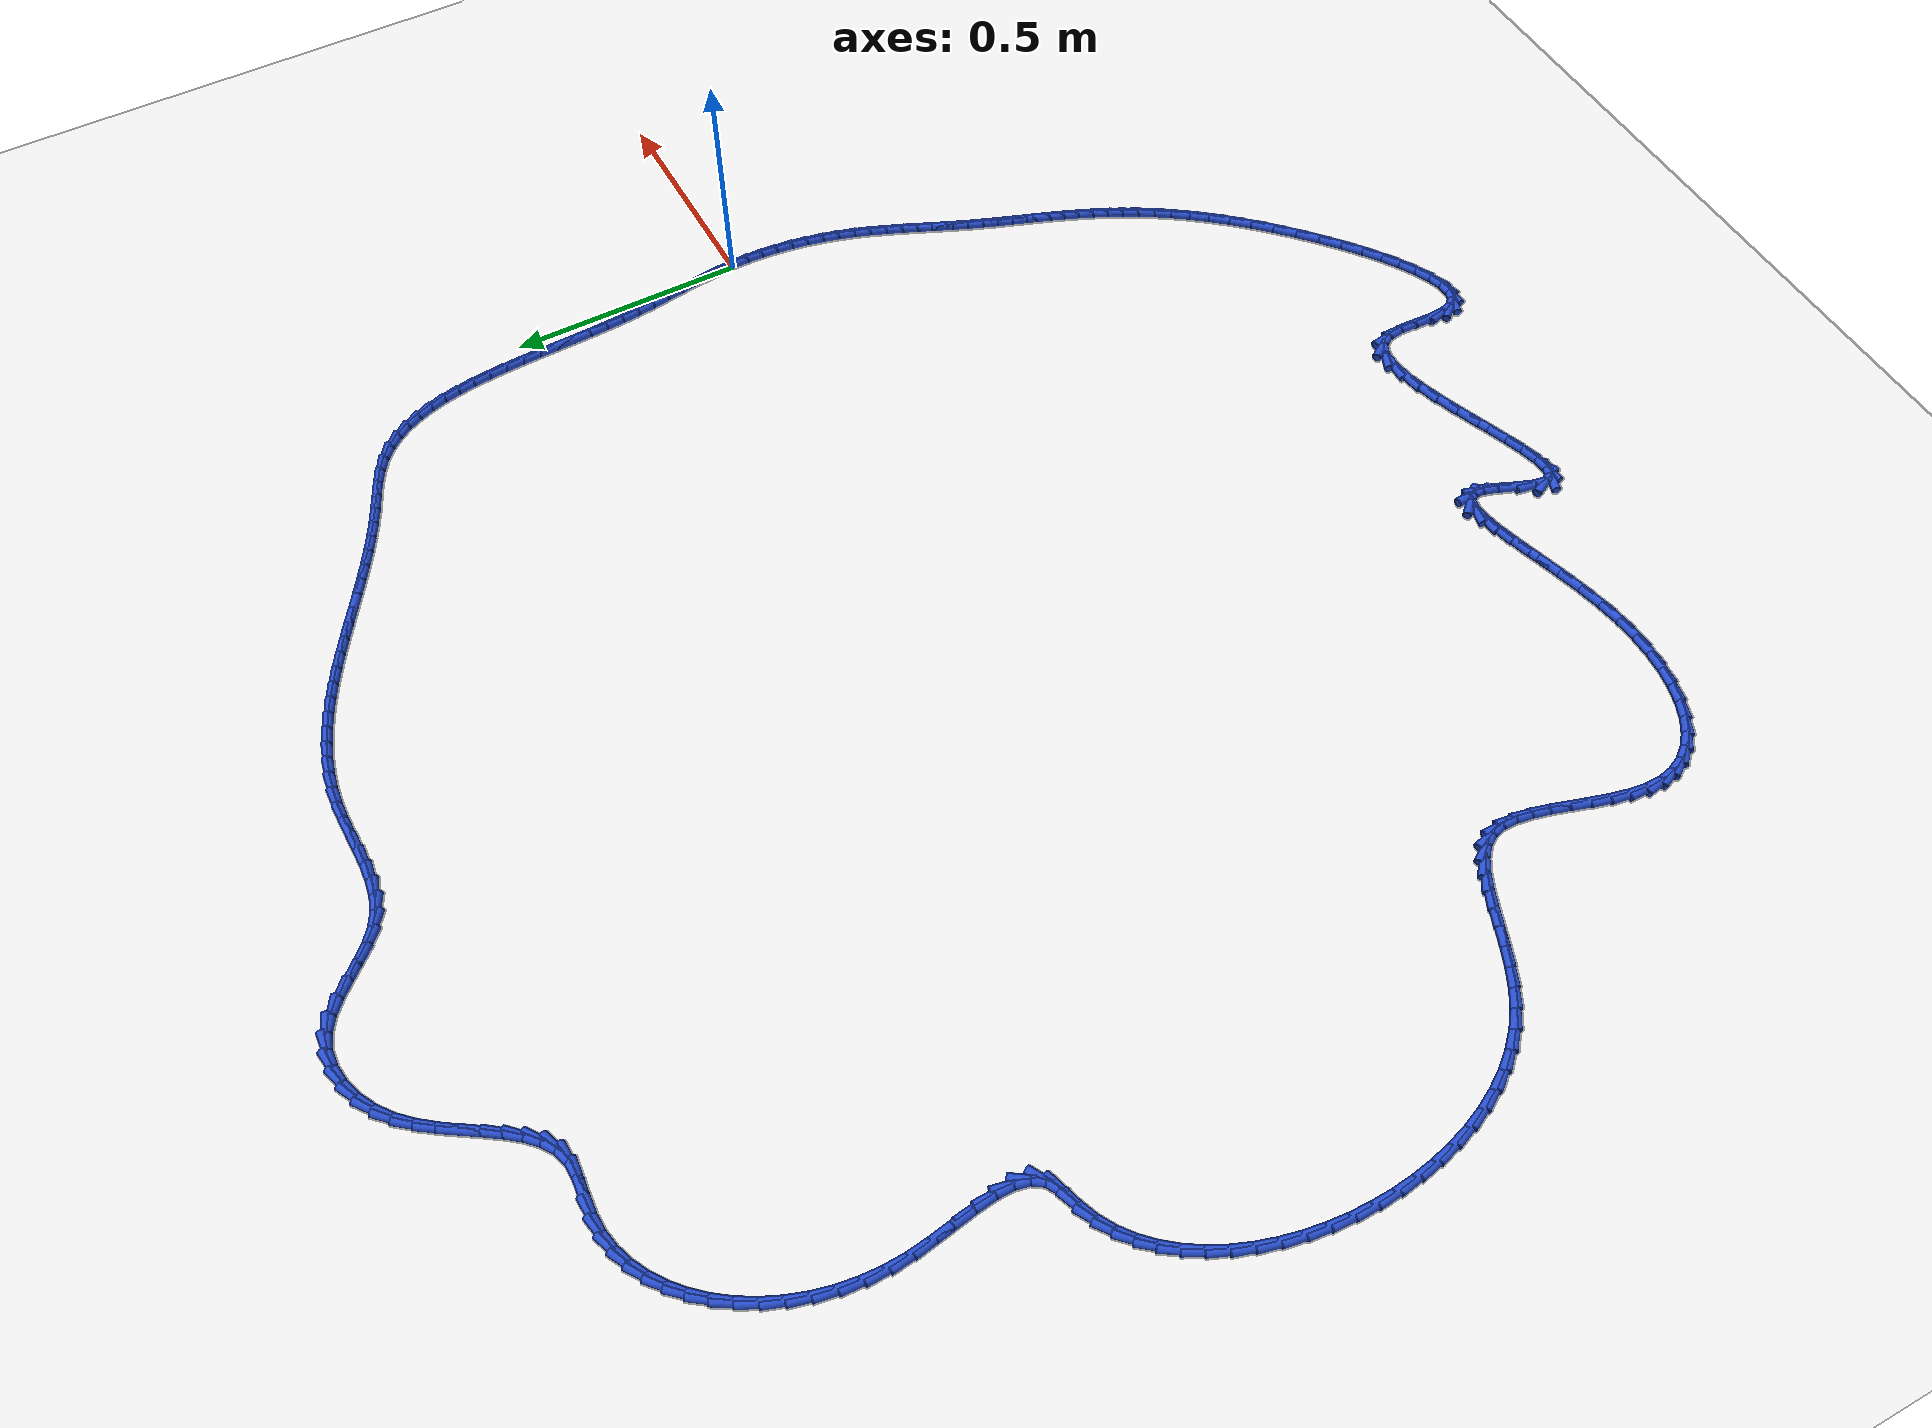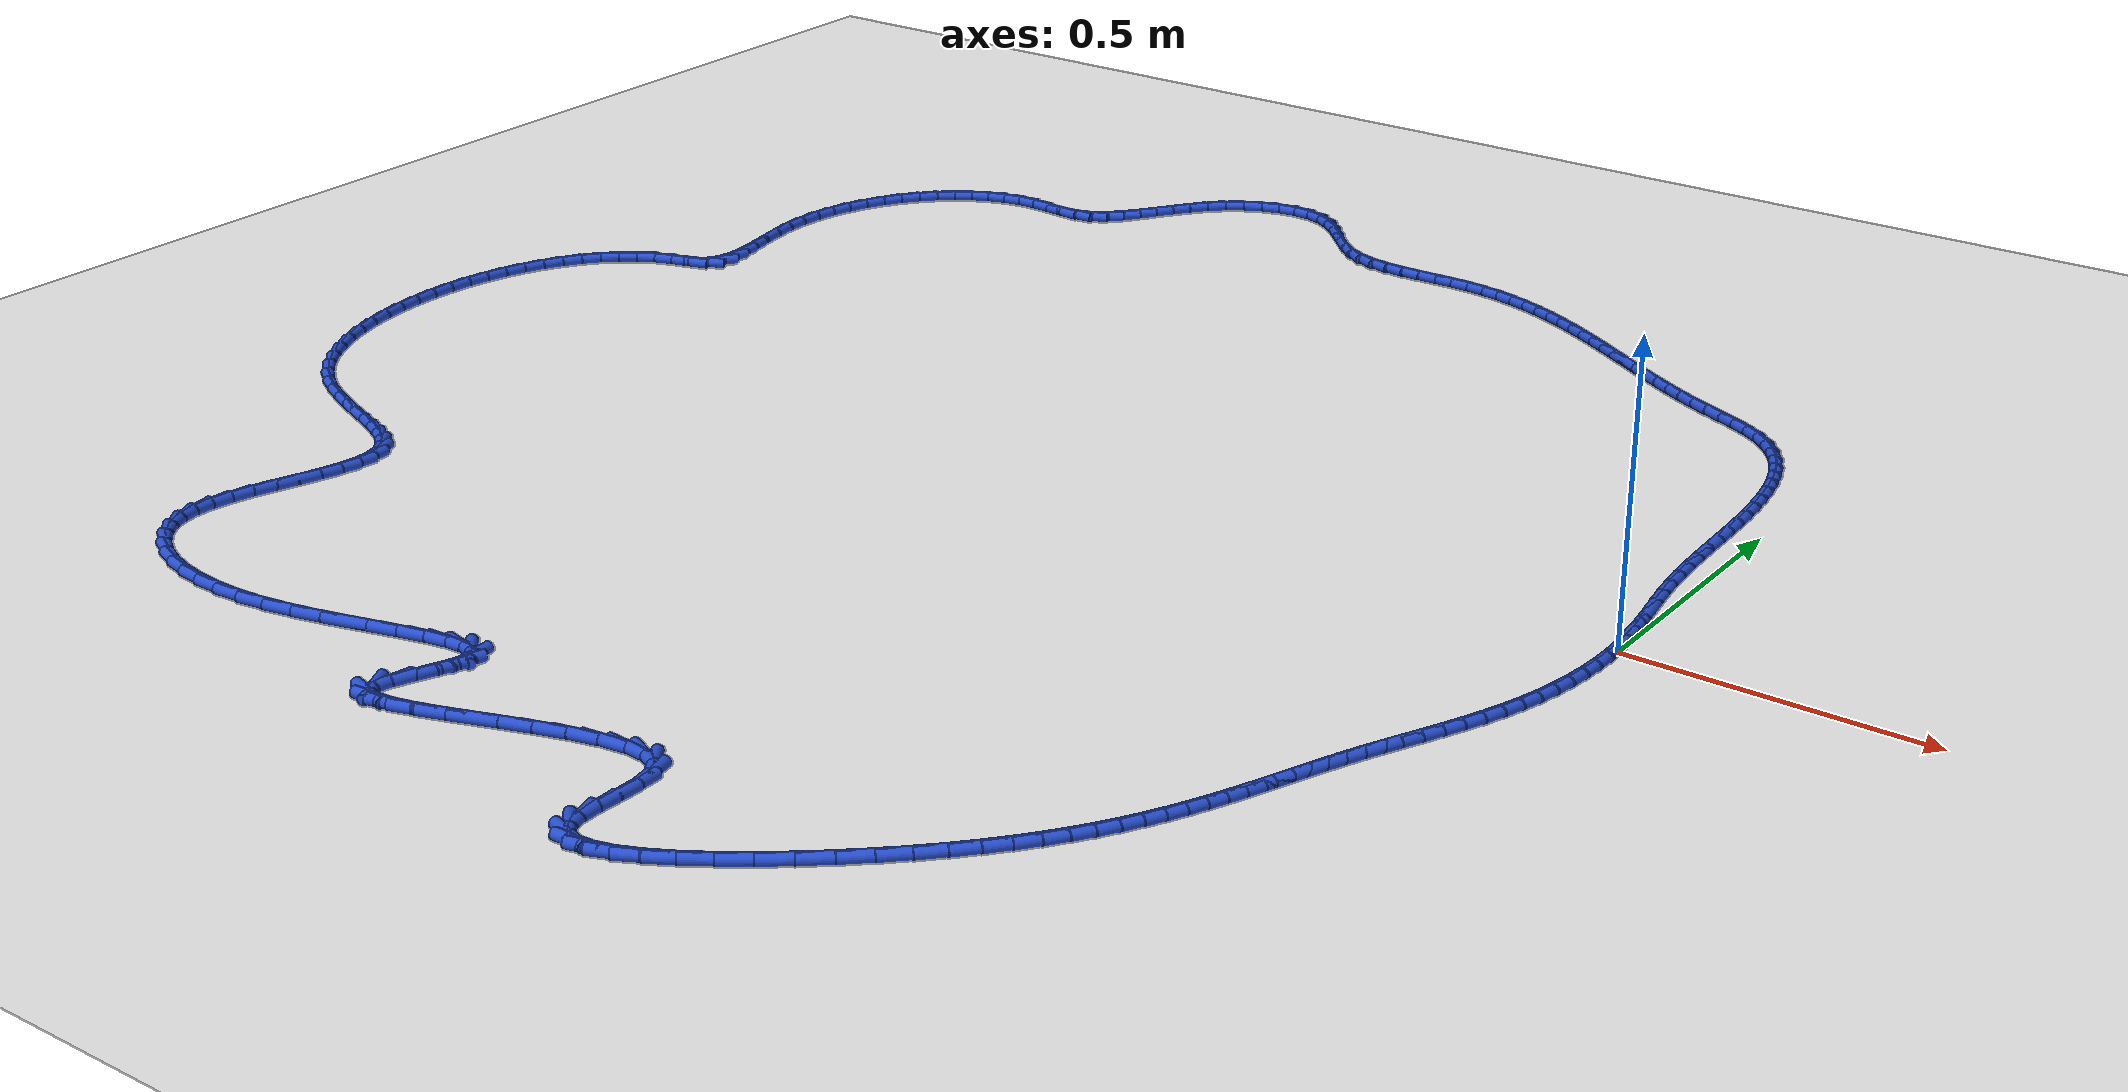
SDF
<sdf version="1.6">
 <world name="default">
  <light name="sun" type="directional">
   <pose>0 0 10 0 -0 0</pose>
   <diffuse>0.8 0.8 0.8 1</diffuse>
   <specular>0.2 0.2 0.2 1</specular>
   <attenuation>
    <range>1000</range>
    <constant>0.9</constant>
    <linear>0.01</linear>
    <quadratic>0.001</quadratic>
   </attenuation>
   <direction>-0.5 0.1 -0.9</direction>
  </light>
  <model name="ground_plane">
   <static>1</static>
   <link name="link">
    <collision name="collision">
     <geometry><plane><normal>0 0 1</normal><size>100 100</size></plane></geometry>
     <surface><friction><ode><mu>100</mu><mu2>50</mu2></ode></friction></surface>
    </collision>
    <visual name="visual">
     <cast_shadows>0</cast_shadows>
     <geometry><plane><normal>0 0 1</normal><size>100 100</size></plane></geometry>
     <material>
      <script><uri>file://media/materials/scripts/gazebo.material</uri><name>Gazebo/WhiteGlow</name></script>
     </material>
    </visual>
   </link>
  </model>
  <gravity>0 0 -9.8</gravity>
  <magnetic_field>6e-06 2.3e-05 -4.2e-05</magnetic_field>
  <atmosphere type="adiabatic"/>
  <physics name="default_physics" default="0" type="ode">
   <max_step_size>0.001</max_step_size>
   <real_time_factor>1</real_time_factor>
   <real_time_update_rate>1000</real_time_update_rate>
  </physics>
  <scene><ambient>0.4 0.4 0.4 1</ambient><background>0.7 0.7 0.7 1</background><shadows>1</shadows></scene>
  <spherical_coordinates>
   <surface_model>EARTH_WGS84</surface_model>
   <latitude_deg>0</latitude_deg>
   <longitude_deg>0</longitude_deg>
   <elevation>0</elevation>
   <heading_deg>0</heading_deg>
  </spherical_coordinates>
  <model name="line">
   <link name="link_0">
    <pose>1.734723475976807e-18 6.938893903907228e-17 0.01 0 1.57 -1.49729034495382</pose>
    <collision name="collision">
     <geometry><cylinder><radius>0.01</radius><length>0.08</length></cylinder></geometry>
    </collision>
    <visual name="visual">
     <material>
      <script><name>Gazebo/Blue</name><uri>file://media/materials/scripts/gazebo.material</uri></script>
     </material>
     <geometry><cylinder><radius>0.01</radius><length>0.08</length></cylinder></geometry>
    </visual>
   </link>
   <link name="link_1">
    <pose>-0.0025253900705594695 0.03429435308270315 0.01 0 1.57 -1.4575326165541347</pose>
    <collision name="collision">
     <geometry><cylinder><radius>0.01</radius><length>0.08</length></cylinder></geometry>
    </collision>
    <visual name="visual">
     <material>
      <script><name>Gazebo/Blue</name><uri>file://media/materials/scripts/gazebo.material</uri></script>
     </material>
     <geometry><cylinder><radius>0.01</radius><length>0.08</length></cylinder></geometry>
    </visual>
   </link>
   <link name="link_2">
    <pose>-0.006405219080018926 0.06840257522807053 0.01 0 1.57 -1.4298699594663284</pose>
    <collision name="collision">
     <geometry><cylinder><radius>0.01</radius><length>0.08</length></cylinder></geometry>
    </collision>
    <visual name="visual">
     <material>
      <script><name>Gazebo/Blue</name><uri>file://media/materials/scripts/gazebo.material</uri></script>
     </material>
     <geometry><cylinder><radius>0.01</radius><length>0.08</length></cylinder></geometry>
    </visual>
   </link>
   <link name="link_3">
    <pose>-0.011245025473110617 0.10251772397805181 0.01 0 1.57 -1.4145600217892622</pose>
    <collision name="collision">
     <geometry><cylinder><radius>0.01</radius><length>0.08</length></cylinder></geometry>
    </collision>
    <visual name="visual">
     <material>
      <script><name>Gazebo/Blue</name><uri>file://media/materials/scripts/gazebo.material</uri></script>
     </material>
     <geometry><cylinder><radius>0.01</radius><length>0.08</length></cylinder></geometry>
    </visual>
   </link>
   <link name="link_4">
    <pose>-0.016650347694566796 0.13683285687459656 0.01 0 1.57 -1.411493078600787</pose>
    <collision name="collision">
     <geometry><cylinder><radius>0.01</radius><length>0.08</length></cylinder></geometry>
    </collision>
    <visual name="visual">
     <material>
      <script><name>Gazebo/Blue</name><uri>file://media/materials/scripts/gazebo.material</uri></script>
     </material>
     <geometry><cylinder><radius>0.01</radius><length>0.08</length></cylinder></geometry>
    </visual>
   </link>
   <link name="link_5">
    <pose>-0.02222672418911971 0.1715410314596543 0.01 0 1.57 -1.4202766667233289</pose>
    <collision name="collision">
     <geometry><cylinder><radius>0.01</radius><length>0.08</length></cylinder></geometry>
    </collision>
    <visual name="visual">
     <material>
      <script><name>Gazebo/Blue</name><uri>file://media/materials/scripts/gazebo.material</uri></script>
     </material>
     <geometry><cylinder><radius>0.01</radius><length>0.08</length></cylinder></geometry>
    </visual>
   </link>
   <link name="link_6">
    <pose>-0.027579693401501622 0.2068353052751747 0.01 0 1.57 -1.4402796867522307</pose>
    <collision name="collision">
     <geometry><cylinder><radius>0.01</radius><length>0.08</length></cylinder></geometry>
    </collision>
    <visual name="visual">
     <material>
      <script><name>Gazebo/Blue</name><uri>file://media/materials/scripts/gazebo.material</uri></script>
     </material>
     <geometry><cylinder><radius>0.01</radius><length>0.08</length></cylinder></geometry>
    </visual>
   </link>
   <link name="link_7">
    <pose>-0.032314793776444764 0.24290873586310724 0.01 0 1.57 -1.4700609311337094</pose>
    <collision name="collision">
     <geometry><cylinder><radius>0.01</radius><length>0.08</length></cylinder></geometry>
    </collision>
    <visual name="visual">
     <material>
      <script><name>Gazebo/Blue</name><uri>file://media/materials/scripts/gazebo.material</uri></script>
     </material>
     <geometry><cylinder><radius>0.01</radius><length>0.08</length></cylinder></geometry>
    </visual>
   </link>
   <link name="link_8">
    <pose>-0.036057974832030236 0.2799415086800802 0.01 0 1.57 -1.4990809527026274</pose>
    <collision name="collision">
     <geometry><cylinder><radius>0.01</radius><length>0.08</length></cylinder></geometry>
    </collision>
    <visual name="visual">
     <material>
      <script><name>Gazebo/Blue</name><uri>file://media/materials/scripts/gazebo.material</uri></script>
     </material>
     <geometry><cylinder><radius>0.01</radius><length>0.08</length></cylinder></geometry>
    </visual>
   </link>
   <link name="link_9">
    <pose>-0.038784397628216255 0.3178935816285214 0.01 0 1.57 -1.51965966266096</pose>
    <collision name="collision">
     <geometry><cylinder><radius>0.01</radius><length>0.08</length></cylinder></geometry>
    </collision>
    <visual name="visual">
     <material>
      <script><name>Gazebo/Blue</name><uri>file://media/materials/scripts/gazebo.material</uri></script>
     </material>
     <geometry><cylinder><radius>0.01</radius><length>0.08</length></cylinder></geometry>
    </visual>
   </link>
   <link name="link_10">
    <pose>-0.04076237299719372 0.3565400399774797 0.01 0 1.57 -1.5322850215961288</pose>
    <collision name="collision">
     <geometry><cylinder><radius>0.01</radius><length>0.08</length></cylinder></geometry>
    </collision>
    <visual name="visual">
     <material>
      <script><name>Gazebo/Blue</name><uri>file://media/materials/scripts/gazebo.material</uri></script>
     </material>
     <geometry><cylinder><radius>0.01</radius><length>0.08</length></cylinder></geometry>
    </visual>
   </link>
   <link name="link_11">
    <pose>-0.04226930274641852 0.39565023584286313 0.01 0 1.57 -1.5374285366922666</pose>
    <collision name="collision">
     <geometry><cylinder><radius>0.01</radius><length>0.08</length></cylinder></geometry>
    </collision>
    <visual name="visual">
     <material>
      <script><name>Gazebo/Blue</name><uri>file://media/materials/scripts/gazebo.material</uri></script>
     </material>
     <geometry><cylinder><radius>0.01</radius><length>0.08</length></cylinder></geometry>
    </visual>
   </link>
   <link name="link_12">
    <pose>-0.04358258868334654 0.43499352134058056 0.01 0 1.57 -1.5353043592740523</pose>
    <collision name="collision">
     <geometry><cylinder><radius>0.01</radius><length>0.08</length></cylinder></geometry>
    </collision>
    <visual name="visual">
     <material>
      <script><name>Gazebo/Blue</name><uri>file://media/materials/scripts/gazebo.material</uri></script>
     </material>
     <geometry><cylinder><radius>0.01</radius><length>0.08</length></cylinder></geometry>
    </visual>
   </link>
   <link name="link_13">
    <pose>-0.0449796326154337 0.4743392485865402 0.01 0 1.57 -1.5258798510124978</pose>
    <collision name="collision">
     <geometry><cylinder><radius>0.01</radius><length>0.08</length></cylinder></geometry>
    </collision>
    <visual name="visual">
     <material>
      <script><name>Gazebo/Blue</name><uri>file://media/materials/scripts/gazebo.material</uri></script>
     </material>
     <geometry><cylinder><radius>0.01</radius><length>0.08</length></cylinder></geometry>
    </visual>
   </link>
   <link name="link_14">
    <pose>-0.04673783635013589 0.5134567696966504 0.01 0 1.57 -1.5088774424410398</pose>
    <collision name="collision">
     <geometry><cylinder><radius>0.01</radius><length>0.08</length></cylinder></geometry>
    </collision>
    <visual name="visual">
     <material>
      <script><name>Gazebo/Blue</name><uri>file://media/materials/scripts/gazebo.material</uri></script>
     </material>
     <geometry><cylinder><radius>0.01</radius><length>0.08</length></cylinder></geometry>
    </visual>
   </link>
   <link name="link_15">
    <pose>-0.04913460169490902 0.5521154367868201 0.01 0 1.57 -1.483768834291413</pose>
    <collision name="collision">
     <geometry><cylinder><radius>0.01</radius><length>0.08</length></cylinder></geometry>
    </collision>
    <visual name="visual">
     <material>
      <script><name>Gazebo/Blue</name><uri>file://media/materials/scripts/gazebo.material</uri></script>
     </material>
     <geometry><cylinder><radius>0.01</radius><length>0.08</length></cylinder></geometry>
    </visual>
   </link>
   <link name="link_16">
    <pose>-0.052447330457208965 0.5900846019729572 0.01 0 1.57 -1.4497655786482748</pose>
    <collision name="collision">
     <geometry><cylinder><radius>0.01</radius><length>0.08</length></cylinder></geometry>
    </collision>
    <visual name="visual">
     <material>
      <script><name>Gazebo/Blue</name><uri>file://media/materials/scripts/gazebo.material</uri></script>
     </material>
     <geometry><cylinder><radius>0.01</radius><length>0.08</length></cylinder></geometry>
    </visual>
   </link>
   <link name="link_17">
    <pose>-0.05695342444449163 0.6271336173709703 0.01 0 1.57 -1.4058150263898792</pose>
    <collision name="collision">
     <geometry><cylinder><radius>0.01</radius><length>0.08</length></cylinder></geometry>
    </collision>
    <visual name="visual">
     <material>
      <script><name>Gazebo/Blue</name><uri>file://media/materials/scripts/gazebo.material</uri></script>
     </material>
     <geometry><cylinder><radius>0.01</radius><length>0.08</length></cylinder></geometry>
    </visual>
   </link>
   <link name="link_18">
    <pose>-0.06293028546421292 0.6630318350967679 0.01 0 1.57 -1.350619492227149</pose>
    <collision name="collision">
     <geometry><cylinder><radius>0.01</radius><length>0.08</length></cylinder></geometry>
    </collision>
    <visual name="visual">
     <material>
      <script><name>Gazebo/Blue</name><uri>file://media/materials/scripts/gazebo.material</uri></script>
     </material>
     <geometry><cylinder><radius>0.01</radius><length>0.08</length></cylinder></geometry>
    </visual>
   </link>
   <link name="link_19">
    <pose>-0.07065531532382874 0.6975486072662584 0.01 0 1.57 -1.2827110960851376</pose>
    <collision name="collision">
     <geometry><cylinder><radius>0.01</radius><length>0.08</length></cylinder></geometry>
    </collision>
    <visual name="visual">
     <material>
      <script><name>Gazebo/Blue</name><uri>file://media/materials/scripts/gazebo.material</uri></script>
     </material>
     <geometry><cylinder><radius>0.01</radius><length>0.08</length></cylinder></geometry>
    </visual>
   </link>
   <link name="link_20">
    <pose>-0.08040591583079497 0.7304532859953504 0.01 0 1.57 -1.200634262246339</pose>
    <collision name="collision">
     <geometry><cylinder><radius>0.01</radius><length>0.08</length></cylinder></geometry>
    </collision>
    <visual name="visual">
     <material>
      <script><name>Gazebo/Blue</name><uri>file://media/materials/scripts/gazebo.material</uri></script>
     </material>
     <geometry><cylinder><radius>0.01</radius><length>0.08</length></cylinder></geometry>
    </visual>
   </link>
   <link name="link_21">
    <pose>-0.09245948879256752 0.7615152233999523 0.01 0 1.57 -1.1033015774696588</pose>
    <collision name="collision">
     <geometry><cylinder><radius>0.01</radius><length>0.08</length></cylinder></geometry>
    </collision>
    <visual name="visual">
     <material>
      <script><name>Gazebo/Blue</name><uri>file://media/materials/scripts/gazebo.material</uri></script>
     </material>
     <geometry><cylinder><radius>0.01</radius><length>0.08</length></cylinder></geometry>
    </visual>
   </link>
   <link name="link_22">
    <pose>-0.10709343601660229 0.7905037715959723 0.01 0 1.57 -0.9905636971994166</pose>
    <collision name="collision">
     <geometry><cylinder><radius>0.01</radius><length>0.08</length></cylinder></geometry>
    </collision>
    <visual name="visual">
     <material>
      <script><name>Gazebo/Blue</name><uri>file://media/materials/scripts/gazebo.material</uri></script>
     </material>
     <geometry><cylinder><radius>0.01</radius><length>0.08</length></cylinder></geometry>
    </visual>
   </link>
   <link name="link_23">
    <pose>-0.12458515931035519 0.8171882826993191 0.01 0 1.57 -0.8639140105229496</pose>
    <collision name="collision">
     <geometry><cylinder><radius>0.01</radius><length>0.08</length></cylinder></geometry>
    </collision>
    <visual name="visual">
     <material>
      <script><name>Gazebo/Blue</name><uri>file://media/materials/scripts/gazebo.material</uri></script>
     </material>
     <geometry><cylinder><radius>0.01</radius><length>0.08</length></cylinder></geometry>
    </visual>
   </link>
   <link name="link_24">
    <pose>-0.14521206048128218 0.8413381088259013 0.01 0 1.57 -0.7270155489127893</pose>
    <collision name="collision">
     <geometry><cylinder><radius>0.01</radius><length>0.08</length></cylinder></geometry>
    </collision>
    <visual name="visual">
     <material>
      <script><name>Gazebo/Blue</name><uri>file://media/materials/scripts/gazebo.material</uri></script>
     </material>
     <geometry><cylinder><radius>0.01</radius><length>0.08</length></cylinder></geometry>
    </visual>
   </link>
   <link name="link_25">
    <pose>-0.169251541336839 0.862722602091627 0.01 0 1.57 -0.5903654275370994</pose>
    <collision name="collision">
     <geometry><cylinder><radius>0.01</radius><length>0.08</length></cylinder></geometry>
    </collision>
    <visual name="visual">
     <material>
      <script><name>Gazebo/Blue</name><uri>file://media/materials/scripts/gazebo.material</uri></script>
     </material>
     <geometry><cylinder><radius>0.01</radius><length>0.08</length></cylinder></geometry>
    </visual>
   </link>
   <link name="link_26">
    <pose>-0.19686103406386943 0.8812233097342668 0.01 0 1.57 -0.4906588559922567</pose>
    <collision name="collision">
     <geometry><cylinder><radius>0.01</radius><length>0.08</length></cylinder></geometry>
    </collision>
    <visual name="visual">
     <material>
      <script><name>Gazebo/Blue</name><uri>file://media/materials/scripts/gazebo.material</uri></script>
     </material>
     <geometry><cylinder><radius>0.01</radius><length>0.08</length></cylinder></geometry>
    </visual>
   </link>
   <link name="link_27">
    <pose>-0.22735219356879652 0.8975127466095674 0.01 0 1.57 -0.43682327546118427</pose>
    <collision name="collision">
     <geometry><cylinder><radius>0.01</radius><length>0.08</length></cylinder></geometry>
    </collision>
    <visual name="visual">
     <material>
      <script><name>Gazebo/Blue</name><uri>file://media/materials/scripts/gazebo.material</uri></script>
     </material>
     <geometry><cylinder><radius>0.01</radius><length>0.08</length></cylinder></geometry>
    </visual>
   </link>
   <link name="link_28">
    <pose>-0.259673018149431 0.9126035178170462 0.01 0 1.57 -0.4231640305605351</pose>
    <collision name="collision">
     <geometry><cylinder><radius>0.01</radius><length>0.08</length></cylinder></geometry>
    </collision>
    <visual name="visual">
     <material>
      <script><name>Gazebo/Blue</name><uri>file://media/materials/scripts/gazebo.material</uri></script>
     </material>
     <geometry><cylinder><radius>0.01</radius><length>0.08</length></cylinder></geometry>
    </visual>
   </link>
   <link name="link_29">
    <pose>-0.2927700964962224 0.9275095467155354 0.01 0 1.57 -0.44528197395674884</pose>
    <collision name="collision">
     <geometry><cylinder><radius>0.01</radius><length>0.08</length></cylinder></geometry>
    </collision>
    <visual name="visual">
     <material>
      <script><name>Gazebo/Blue</name><uri>file://media/materials/scripts/gazebo.material</uri></script>
     </material>
     <geometry><cylinder><radius>0.01</radius><length>0.08</length></cylinder></geometry>
    </visual>
   </link>
   <link name="link_30">
    <pose>-0.325636802048556 0.9431951593816497 0.01 0 1.57 -0.47921975140571127</pose>
    <collision name="collision">
     <geometry><cylinder><radius>0.01</radius><length>0.08</length></cylinder></geometry>
    </collision>
    <visual name="visual">
     <material>
      <script><name>Gazebo/Blue</name><uri>file://media/materials/scripts/gazebo.material</uri></script>
     </material>
     <geometry><cylinder><radius>0.01</radius><length>0.08</length></cylinder></geometry>
    </visual>
   </link>
   <link name="link_31">
    <pose>-0.3578957967348545 0.9599575628094738 0.01 0 1.57 -0.507915673638968</pose>
    <collision name="collision">
     <geometry><cylinder><radius>0.01</radius><length>0.08</length></cylinder></geometry>
    </collision>
    <visual name="visual">
     <material>
      <script><name>Gazebo/Blue</name><uri>file://media/materials/scripts/gazebo.material</uri></script>
     </material>
     <geometry><cylinder><radius>0.01</radius><length>0.08</length></cylinder></geometry>
    </visual>
   </link>
   <link name="link_32">
    <pose>-0.3896203573262975 0.9776162597831655 0.01 0 1.57 -0.5309661247453427</pose>
    <collision name="collision">
     <geometry><cylinder><radius>0.01</radius><length>0.08</length></cylinder></geometry>
    </collision>
    <visual name="visual">
     <material>
      <script><name>Gazebo/Blue</name><uri>file://media/materials/scripts/gazebo.material</uri></script>
     </material>
     <geometry><cylinder><radius>0.01</radius><length>0.08</length></cylinder></geometry>
    </visual>
   </link>
   <link name="link_33">
    <pose>-0.42089355643501425 0.9959803683546918 0.01 0 1.57 -0.5483680764258985</pose>
    <collision name="collision">
     <geometry><cylinder><radius>0.01</radius><length>0.08</length></cylinder></geometry>
    </collision>
    <visual name="visual">
     <material>
      <script><name>Gazebo/Blue</name><uri>file://media/materials/scripts/gazebo.material</uri></script>
     </material>
     <geometry><cylinder><radius>0.01</radius><length>0.08</length></cylinder></geometry>
    </visual>
   </link>
   <link name="link_34">
    <pose>-0.4517984666731342 1.0148590065760208 0.01 0 1.57 -0.5601238442951624</pose>
    <collision name="collision">
     <geometry><cylinder><radius>0.01</radius><length>0.08</length></cylinder></geometry>
    </collision>
    <visual name="visual">
     <material>
      <script><name>Gazebo/Blue</name><uri>file://media/materials/scripts/gazebo.material</uri></script>
     </material>
     <geometry><cylinder><radius>0.01</radius><length>0.08</length></cylinder></geometry>
    </visual>
   </link>
   <link name="link_35">
    <pose>-0.48241816065278764 1.0340612924991217 0.01 0 1.57 -0.5662242920693836</pose>
    <collision name="collision">
     <geometry><cylinder><radius>0.01</radius><length>0.08</length></cylinder></geometry>
    </collision>
    <visual name="visual">
     <material>
      <script><name>Gazebo/Blue</name><uri>file://media/materials/scripts/gazebo.material</uri></script>
     </material>
     <geometry><cylinder><radius>0.01</radius><length>0.08</length></cylinder></geometry>
    </visual>
   </link>
   <link name="link_36">
    <pose>-0.5128357109861038 1.0533963441759617 0.01 0 1.57 -0.5666372423448269</pose>
    <collision name="collision">
     <geometry><cylinder><radius>0.01</radius><length>0.08</length></cylinder></geometry>
    </collision>
    <visual name="visual">
     <material>
      <script><name>Gazebo/Blue</name><uri>file://media/materials/scripts/gazebo.material</uri></script>
     </material>
     <geometry><cylinder><radius>0.01</radius><length>0.08</length></cylinder></geometry>
    </visual>
   </link>
   <link name="link_37">
    <pose>-0.5431341902852126 1.0726732796585092 0.01 0 1.57 -0.5613009325293503</pose>
    <collision name="collision">
     <geometry><cylinder><radius>0.01</radius><length>0.08</length></cylinder></geometry>
    </collision>
    <visual name="visual">
     <material>
      <script><name>Gazebo/Blue</name><uri>file://media/materials/scripts/gazebo.material</uri></script>
     </material>
     <geometry><cylinder><radius>0.01</radius><length>0.08</length></cylinder></geometry>
    </visual>
   </link>
   <link name="link_38">
    <pose>-0.5733966711622434 1.0917012169987323 0.01 0 1.57 -0.550122548962029</pose>
    <collision name="collision">
     <geometry><cylinder><radius>0.01</radius><length>0.08</length></cylinder></geometry>
    </collision>
    <visual name="visual">
     <material>
      <script><name>Gazebo/Blue</name><uri>file://media/materials/scripts/gazebo.material</uri></script>
     </material>
     <geometry><cylinder><radius>0.01</radius><length>0.08</length></cylinder></geometry>
    </visual>
   </link>
   <link name="link_39">
    <pose>-0.6037062262293262 1.1102892742485995 0.01 0 1.57 -0.5329822296605902</pose>
    <collision name="collision">
     <geometry><cylinder><radius>0.01</radius><length>0.08</length></cylinder></geometry>
    </collision>
    <visual name="visual">
     <material>
      <script><name>Gazebo/Blue</name><uri>file://media/materials/scripts/gazebo.material</uri></script>
     </material>
     <geometry><cylinder><radius>0.01</radius><length>0.08</length></cylinder></geometry>
    </visual>
   </link>
   <link name="link_40">
    <pose>-0.6341459280985905 1.1282465694600792 0.01 0 1.57 -0.5097433400999187</pose>
    <collision name="collision">
     <geometry><cylinder><radius>0.01</radius><length>0.08</length></cylinder></geometry>
    </collision>
    <visual name="visual">
     <material>
      <script><name>Gazebo/Blue</name><uri>file://media/materials/scripts/gazebo.material</uri></script>
     </material>
     <geometry><cylinder><radius>0.01</radius><length>0.08</length></cylinder></geometry>
    </visual>
   </link>
   <link name="link_41">
    <pose>-0.6647988493821662 1.1453822206851383 0.01 0 1.57 -0.4802701674608907</pose>
    <collision name="collision">
     <geometry><cylinder><radius>0.01</radius><length>0.08</length></cylinder></geometry>
    </collision>
    <visual name="visual">
     <material>
      <script><name>Gazebo/Blue</name><uri>file://media/materials/scripts/gazebo.material</uri></script>
     </material>
     <geometry><cylinder><radius>0.01</radius><length>0.08</length></cylinder></geometry>
    </visual>
   </link>
   <link name="link_42">
    <pose>-0.6957480626921826 1.1615053459757465 0.01 0 1.57 -0.44445425658547955</pose>
    <collision name="collision">
     <geometry><cylinder><radius>0.01</radius><length>0.08</length></cylinder></geometry>
    </collision>
    <visual name="visual">
     <material>
      <script><name>Gazebo/Blue</name><uri>file://media/materials/scripts/gazebo.material</uri></script>
     </material>
     <geometry><cylinder><radius>0.01</radius><length>0.08</length></cylinder></geometry>
    </visual>
   </link>
   <link name="link_43">
    <pose>-0.7270766406407698 1.1764250633838707 0.01 0 1.57 -0.40225014596360037</pose>
    <collision name="collision">
     <geometry><cylinder><radius>0.01</radius><length>0.08</length></cylinder></geometry>
    </collision>
    <visual name="visual">
     <material>
      <script><name>Gazebo/Blue</name><uri>file://media/materials/scripts/gazebo.material</uri></script>
     </material>
     <geometry><cylinder><radius>0.01</radius><length>0.08</length></cylinder></geometry>
    </visual>
   </link>
   <link name="link_44">
    <pose>-0.758867655840057 1.18995049096148 0.01 0 1.57 -0.35371990406697174</pose>
    <collision name="collision">
     <geometry><cylinder><radius>0.01</radius><length>0.08</length></cylinder></geometry>
    </collision>
    <visual name="visual">
     <material>
      <script><name>Gazebo/Blue</name><uri>file://media/materials/scripts/gazebo.material</uri></script>
     </material>
     <geometry><cylinder><radius>0.01</radius><length>0.08</length></cylinder></geometry>
    </visual>
   </link>
   <link name="link_45">
    <pose>-0.7912041809021746 1.2018907467605422 0.01 0 1.57 -0.2990833196702616</pose>
    <collision name="collision">
     <geometry><cylinder><radius>0.01</radius><length>0.08</length></cylinder></geometry>
    </collision>
    <visual name="visual">
     <material>
      <script><name>Gazebo/Blue</name><uri>file://media/materials/scripts/gazebo.material</uri></script>
     </material>
     <geometry><cylinder><radius>0.01</radius><length>0.08</length></cylinder></geometry>
    </visual>
   </link>
   <link name="link_46">
    <pose>-0.8241692884392514 1.2120549488330252 0.01 0 1.57 -0.2387669150535141</pose>
    <collision name="collision">
     <geometry><cylinder><radius>0.01</radius><length>0.08</length></cylinder></geometry>
    </collision>
    <visual name="visual">
     <material>
      <script><name>Gazebo/Blue</name><uri>file://media/materials/scripts/gazebo.material</uri></script>
     </material>
     <geometry><cylinder><radius>0.01</radius><length>0.08</length></cylinder></geometry>
    </visual>
   </link>
   <link name="link_47">
    <pose>-0.8578460510634178 1.2202522152308977 0.01 0 1.57 -0.17344094599628823</pose>
    <collision name="collision">
     <geometry><cylinder><radius>0.01</radius><length>0.08</length></cylinder></geometry>
    </collision>
    <visual name="visual">
     <material>
      <script><name>Gazebo/Blue</name><uri>file://media/materials/scripts/gazebo.material</uri></script>
     </material>
     <geometry><cylinder><radius>0.01</radius><length>0.08</length></cylinder></geometry>
    </visual>
   </link>
   <link name="link_48">
    <pose>-0.8923175413868033 1.2262916640061274 0.01 0 1.57 -0.10403109041895171</pose>
    <collision name="collision">
     <geometry><cylinder><radius>0.01</radius><length>0.08</length></cylinder></geometry>
    </collision>
    <visual name="visual">
     <material>
      <script><name>Gazebo/Blue</name><uri>file://media/materials/scripts/gazebo.material</uri></script>
     </material>
     <geometry><cylinder><radius>0.01</radius><length>0.08</length></cylinder></geometry>
    </visual>
   </link>
   <link name="link_49">
    <pose>-0.9276668320215371 1.2299824132106827 0.01 0 1.57 -0.03492770932390305</pose>
    <collision name="collision">
     <geometry><cylinder><radius>0.01</radius><length>0.08</length></cylinder></geometry>
    </collision>
    <visual name="visual">
     <material>
      <script><name>Gazebo/Blue</name><uri>file://media/materials/scripts/gazebo.material</uri></script>
     </material>
     <geometry><cylinder><radius>0.01</radius><length>0.08</length></cylinder></geometry>
    </visual>
   </link>
   <link name="link_50">
    <pose>-0.9639287901547265 1.2312494756345558 0.01 0 1.57 0.00949308391064835</pose>
    <collision name="collision">
     <geometry><cylinder><radius>0.01</radius><length>0.08</length></cylinder></geometry>
    </collision>
    <visual name="visual">
     <material>
      <script><name>Gazebo/Blue</name><uri>file://media/materials/scripts/gazebo.material</uri></script>
     </material>
     <geometry><cylinder><radius>0.01</radius><length>0.08</length></cylinder></geometry>
    </visual>
   </link>
   <link name="link_51">
    <pose>-1.000771484897298 1.230899714335136 0.01 0 1.57 0.02042746529366963</pose>
    <collision name="collision">
     <geometry><cylinder><radius>0.01</radius><length>0.08</length></cylinder></geometry>
    </collision>
    <visual name="visual">
     <material>
      <script><name>Gazebo/Blue</name><uri>file://media/materials/scripts/gazebo.material</uri></script>
     </material>
     <geometry><cylinder><radius>0.01</radius><length>0.08</length></cylinder></geometry>
    </visual>
   </link>
   <link name="link_52">
    <pose>-1.0376943726680934 1.2301453683989096 0.01 0 1.57 -0.0015190542157227352</pose>
    <collision name="collision">
     <geometry><cylinder><radius>0.01</radius><length>0.08</length></cylinder></geometry>
    </collision>
    <visual name="visual">
     <material>
      <script><name>Gazebo/Blue</name><uri>file://media/materials/scripts/gazebo.material</uri></script>
     </material>
     <geometry><cylinder><radius>0.01</radius><length>0.08</length></cylinder></geometry>
    </visual>
   </link>
   <link name="link_53">
    <pose>-1.0741960199748943 1.2302008164227811 0.01 0 1.57 -0.05838440200083776</pose>
    <collision name="collision">
     <geometry><cylinder><radius>0.01</radius><length>0.08</length></cylinder></geometry>
    </collision>
    <visual name="visual">
     <material>
      <script><name>Gazebo/Blue</name><uri>file://media/materials/scripts/gazebo.material</uri></script>
     </material>
     <geometry><cylinder><radius>0.01</radius><length>0.08</length></cylinder></geometry>
    </visual>
   </link>
   <link name="link_54">
    <pose>-1.1097749933254841 1.2322804370036562 0.01 0 1.57 -0.15446721152338902</pose>
    <collision name="collision">
     <geometry><cylinder><radius>0.01</radius><length>0.08</length></cylinder></geometry>
    </collision>
    <visual name="visual">
     <material>
      <script><name>Gazebo/Blue</name><uri>file://media/materials/scripts/gazebo.material</uri></script>
     </material>
     <geometry><cylinder><radius>0.01</radius><length>0.08</length></cylinder></geometry>
    </visual>
   </link>
   <link name="link_55">
    <pose>-1.1439298592276441 1.2375986087384387 0.01 0 1.57 -0.2943664020281546</pose>
    <collision name="collision">
     <geometry><cylinder><radius>0.01</radius><length>0.08</length></cylinder></geometry>
    </collision>
    <visual name="visual">
     <material>
      <script><name>Gazebo/Blue</name><uri>file://media/materials/scripts/gazebo.material</uri></script>
     </material>
     <geometry><cylinder><radius>0.01</radius><length>0.08</length></cylinder></geometry>
    </visual>
   </link>
   <link name="link_56">
    <pose>-1.176159184189157 1.2473697102240342 0.01 0 1.57 -0.4778142915954791</pose>
    <collision name="collision">
     <geometry><cylinder><radius>0.01</radius><length>0.08</length></cylinder></geometry>
    </collision>
    <visual name="visual">
     <material>
      <script><name>Gazebo/Blue</name><uri>file://media/materials/scripts/gazebo.material</uri></script>
     </material>
     <geometry><cylinder><radius>0.01</radius><length>0.08</length></cylinder></geometry>
    </visual>
   </link>
   <link name="link_57">
    <pose>-1.2059635126294983 1.262803460992066 0.01 0 1.57 -0.6628788269033995</pose>
    <collision name="collision">
     <geometry><cylinder><radius>0.01</radius><length>0.08</length></cylinder></geometry>
    </collision>
    <visual name="visual">
     <material>
      <script><name>Gazebo/Blue</name><uri>file://media/materials/scripts/gazebo.material</uri></script>
     </material>
     <geometry><cylinder><radius>0.01</radius><length>0.08</length></cylinder></geometry>
    </visual>
   </link>
   <link name="link_58">
    <pose>-1.233264348280855 1.2841179908455744 0.01 0 1.57 -0.7763594942866026</pose>
    <collision name="collision">
     <geometry><cylinder><radius>0.01</radius><length>0.08</length></cylinder></geometry>
    </collision>
    <visual name="visual">
     <material>
      <script><name>Gazebo/Blue</name><uri>file://media/materials/scripts/gazebo.material</uri></script>
     </material>
     <geometry><cylinder><radius>0.01</radius><length>0.08</length></cylinder></geometry>
    </visual>
   </link>
   <link name="link_59">
    <pose>-1.2589232183705352 1.3093171594331292 0.01 0 1.57 -0.8197908009743567</pose>
    <collision name="collision">
     <geometry><cylinder><radius>0.01</radius><length>0.08</length></cylinder></geometry>
    </collision>
    <visual name="visual">
     <material>
      <script><name>Gazebo/Blue</name><uri>file://media/materials/scripts/gazebo.material</uri></script>
     </material>
     <geometry><cylinder><radius>0.01</radius><length>0.08</length></cylinder></geometry>
    </visual>
   </link>
   <link name="link_60">
    <pose>-1.2839289667337834 1.3361049260640108 0.01 0 1.57 -0.7997656641673492</pose>
    <collision name="collision">
     <geometry><cylinder><radius>0.01</radius><length>0.08</length></cylinder></geometry>
    </collision>
    <visual name="visual">
     <material>
      <script><name>Gazebo/Blue</name><uri>file://media/materials/scripts/gazebo.material</uri></script>
     </material>
     <geometry><cylinder><radius>0.01</radius><length>0.08</length></cylinder></geometry>
    </visual>
   </link>
   <link name="link_61">
    <pose>-1.3092704372058446 1.3621852500474994 0.01 0 1.57 -0.7133680254018131</pose>
    <collision name="collision">
     <geometry><cylinder><radius>0.01</radius><length>0.08</length></cylinder></geometry>
    </collision>
    <visual name="visual">
     <material>
      <script><name>Gazebo/Blue</name><uri>file://media/materials/scripts/gazebo.material</uri></script>
     </material>
     <geometry><cylinder><radius>0.01</radius><length>0.08</length></cylinder></geometry>
    </visual>
   </link>
   <link name="link_62">
    <pose>-1.3359364736219639 1.3852620906928759 0.01 0 1.57 -0.5502474265232398</pose>
    <collision name="collision">
     <geometry><cylinder><radius>0.01</radius><length>0.08</length></cylinder></geometry>
    </collision>
    <visual name="visual">
     <material>
      <script><name>Gazebo/Blue</name><uri>file://media/materials/scripts/gazebo.material</uri></script>
     </material>
     <geometry><cylinder><radius>0.01</radius><length>0.08</length></cylinder></geometry>
    </visual>
   </link>
   <link name="link_63">
    <pose>-1.364915919817387 1.403039407309422 0.01 0 1.57 -0.3114421813115</pose>
    <collision name="collision">
     <geometry><cylinder><radius>0.01</radius><length>0.08</length></cylinder></geometry>
    </collision>
    <visual name="visual">
     <material>
      <script><name>Gazebo/Blue</name><uri>file://media/materials/scripts/gazebo.material</uri></script>
     </material>
     <geometry><cylinder><radius>0.01</radius><length>0.08</length></cylinder></geometry>
    </visual>
   </link>
   <link name="link_64">
    <pose>-1.397059923987252 1.4133871538379097 0.01 0 1.57 -0.07186729860046163</pose>
    <collision name="collision">
     <geometry><cylinder><radius>0.01</radius><length>0.08</length></cylinder></geometry>
    </collision>
    <visual name="visual">
     <material>
      <script><name>Gazebo/Blue</name><uri>file://media/materials/scripts/gazebo.material</uri></script>
     </material>
     <geometry><cylinder><radius>0.01</radius><length>0.08</length></cylinder></geometry>
    </visual>
   </link>
   <link name="link_65">
    <pose>-1.4317988595312152 1.4158880544159635 0.01 0 1.57 0.13153948399275267</pose>
    <collision name="collision">
     <geometry><cylinder><radius>0.01</radius><length>0.08</length></cylinder></geometry>
    </collision>
    <visual name="visual">
     <material>
      <script><name>Gazebo/Blue</name><uri>file://media/materials/scripts/gazebo.material</uri></script>
     </material>
     <geometry><cylinder><radius>0.01</radius><length>0.08</length></cylinder></geometry>
    </visual>
   </link>
   <link name="link_66">
    <pose>-1.4677252564706045 1.4111348688128897 0.01 0 1.57 0.3091663968761701</pose>
    <collision name="collision">
     <geometry><cylinder><radius>0.01</radius><length>0.08</length></cylinder></geometry>
    </collision>
    <visual name="visual">
     <material>
      <script><name>Gazebo/Blue</name><uri>file://media/materials/scripts/gazebo.material</uri></script>
     </material>
     <geometry><cylinder><radius>0.01</radius><length>0.08</length></cylinder></geometry>
    </visual>
   </link>
   <link name="link_67">
    <pose>-1.503420828905158 1.3997333955907767 0.01 0 1.57 0.473484714630039</pose>
    <collision name="collision">
     <geometry><cylinder><radius>0.01</radius><length>0.08</length></cylinder></geometry>
    </collision>
    <visual name="visual">
     <material>
      <script><name>Gazebo/Blue</name><uri>file://media/materials/scripts/gazebo.material</uri></script>
     </material>
     <geometry><cylinder><radius>0.01</radius><length>0.08</length></cylinder></geometry>
    </visual>
   </link>
   <link name="link_68">
    <pose>-1.537467290934615 1.382289433311711 0.01 0 1.57 0.6359292841784508</pose>
    <collision name="collision">
     <geometry><cylinder><radius>0.01</radius><length>0.08</length></cylinder></geometry>
    </collision>
    <visual name="visual">
     <material>
      <script><name>Gazebo/Blue</name><uri>file://media/materials/scripts/gazebo.material</uri></script>
     </material>
     <geometry><cylinder><radius>0.01</radius><length>0.08</length></cylinder></geometry>
    </visual>
   </link>
   <link name="link_69">
    <pose>-1.5684558865743525 1.3594125485794604 0.01 0 1.57 0.786693013807335</pose>
    <collision name="collision">
     <geometry><cylinder><radius>0.01</radius><length>0.08</length></cylinder></geometry>
    </collision>
    <visual name="visual">
     <material>
      <script><name>Gazebo/Blue</name><uri>file://media/materials/scripts/gazebo.material</uri></script>
     </material>
     <geometry><cylinder><radius>0.01</radius><length>0.08</length></cylinder></geometry>
    </visual>
   </link>
   <link name="link_70">
    <pose>-1.5957714986103875 1.3320261055253844 0.01 0 1.57 0.8947837992267085</pose>
    <collision name="collision">
     <geometry><cylinder><radius>0.01</radius><length>0.08</length></cylinder></geometry>
    </collision>
    <visual name="visual">
     <material>
      <script><name>Gazebo/Blue</name><uri>file://media/materials/scripts/gazebo.material</uri></script>
     </material>
     <geometry><cylinder><radius>0.01</radius><length>0.08</length></cylinder></geometry>
    </visual>
   </link>
   <link name="link_71">
    <pose>-1.6201771908548332 1.3015983884820335 0.01 0 1.57 0.9593526547943908</pose>
    <collision name="collision">
     <geometry><cylinder><radius>0.01</radius><length>0.08</length></cylinder></geometry>
    </collision>
    <visual name="visual">
     <material>
      <script><name>Gazebo/Blue</name><uri>file://media/materials/scripts/gazebo.material</uri></script>
     </material>
     <geometry><cylinder><radius>0.01</radius><length>0.08</length></cylinder></geometry>
    </visual>
   </link>
   <link name="link_72">
    <pose>-1.6425737480313032 1.2696521353735961 0.01 0 1.57 0.9829344865480496</pose>
    <collision name="collision">
     <geometry><cylinder><radius>0.01</radius><length>0.08</length></cylinder></geometry>
    </collision>
    <visual name="visual">
     <material>
      <script><name>Gazebo/Blue</name><uri>file://media/materials/scripts/gazebo.material</uri></script>
     </material>
     <geometry><cylinder><radius>0.01</radius><length>0.08</length></cylinder></geometry>
    </visual>
   </link>
   <link name="link_73">
    <pose>-1.6638619548634106 1.237710084124262 0.01 0 1.57 0.9647178729612463</pose>
    <collision name="collision">
     <geometry><cylinder><radius>0.01</radius><length>0.08</length></cylinder></geometry>
    </collision>
    <visual name="visual">
     <material>
      <script><name>Gazebo/Blue</name><uri>file://media/materials/scripts/gazebo.material</uri></script>
     </material>
     <geometry><cylinder><radius>0.01</radius><length>0.08</length></cylinder></geometry>
    </visual>
   </link>
   <link name="link_74">
    <pose>-1.6849425960747675 1.2072949726582203 0.01 0 1.57 0.8987010847117252</pose>
    <collision name="collision">
     <geometry><cylinder><radius>0.01</radius><length>0.08</length></cylinder></geometry>
    </collision>
    <visual name="visual">
     <material>
      <script><name>Gazebo/Blue</name><uri>file://media/materials/scripts/gazebo.material</uri></script>
     </material>
     <geometry><cylinder><radius>0.01</radius><length>0.08</length></cylinder></geometry>
    </visual>
   </link>
   <link name="link_75">
    <pose>-1.7067164563889878 1.1799295388996611 0.01 0 1.57 0.7729457085765314</pose>
    <collision name="collision">
     <geometry><cylinder><radius>0.01</radius><length>0.08</length></cylinder></geometry>
    </collision>
    <visual name="visual">
     <material>
      <script><name>Gazebo/Blue</name><uri>file://media/materials/scripts/gazebo.material</uri></script>
     </material>
     <geometry><cylinder><radius>0.01</radius><length>0.08</length></cylinder></geometry>
    </visual>
   </link>
   <link name="link_76">
    <pose>-1.7300843205296834 1.1571365207727735 0.01 0 1.57 0.5733013969444873</pose>
    <collision name="collision">
     <geometry><cylinder><radius>0.01</radius><length>0.08</length></cylinder></geometry>
    </collision>
    <visual name="visual">
     <material>
      <script><name>Gazebo/Blue</name><uri>file://media/materials/scripts/gazebo.material</uri></script>
     </material>
     <geometry><cylinder><radius>0.01</radius><length>0.08</length></cylinder></geometry>
    </visual>
   </link>
   <link name="link_77">
    <pose>-1.7559469732204684 1.1404386562017472 0.01 0 1.57 0.30092045713008175</pose>
    <collision name="collision">
     <geometry><cylinder><radius>0.01</radius><length>0.08</length></cylinder></geometry>
    </collision>
    <visual name="visual">
     <material>
      <script><name>Gazebo/Blue</name><uri>file://media/materials/scripts/gazebo.material</uri></script>
     </material>
     <geometry><cylinder><radius>0.01</radius><length>0.08</length></cylinder></geometry>
    </visual>
   </link>
   <link name="link_78">
    <pose>-1.785205135758923 1.1313585296476723 0.01 0 1.57 0.03388666366810367</pose>
    <collision name="collision">
     <geometry><cylinder><radius>0.01</radius><length>0.08</length></cylinder></geometry>
    </collision>
    <visual name="visual">
     <material>
      <script><name>Gazebo/Blue</name><uri>file://media/materials/scripts/gazebo.material</uri></script>
     </material>
     <geometry><cylinder><radius>0.01</radius><length>0.08</length></cylinder></geometry>
    </visual>
   </link>
   <link name="link_79">
    <pose>-1.818271370715437 1.130237596173879 0.01 0 1.57 -0.08825191206194326</pose>
    <collision name="collision">
     <geometry><cylinder><radius>0.01</radius><length>0.08</length></cylinder></geometry>
    </collision>
    <visual name="visual">
     <material>
      <script><name>Gazebo/Blue</name><uri>file://media/materials/scripts/gazebo.material</uri></script>
     </material>
     <geometry><cylinder><radius>0.01</radius><length>0.08</length></cylinder></geometry>
    </visual>
   </link>
   <link name="link_80">
    <pose>-1.8538935572782735 1.1333895092884338 0.01 0 1.57 -0.07860380765954812</pose>
    <collision name="collision">
     <geometry><cylinder><radius>0.01</radius><length>0.08</length></cylinder></geometry>
    </collision>
    <visual name="visual">
     <material>
      <script><name>Gazebo/Blue</name><uri>file://media/materials/scripts/gazebo.material</uri></script>
     </material>
     <geometry><cylinder><radius>0.01</radius><length>0.08</length></cylinder></geometry>
    </visual>
   </link>
   <link name="link_81">
    <pose>-1.8904650389480016 1.1362701020816457 0.01 0 1.57 0.04029579589184466</pose>
    <collision name="collision">
     <geometry><cylinder><radius>0.01</radius><length>0.08</length></cylinder></geometry>
    </collision>
    <visual name="visual">
     <material>
      <script><name>Gazebo/Blue</name><uri>file://media/materials/scripts/gazebo.material</uri></script>
     </material>
     <geometry><cylinder><radius>0.01</radius><length>0.08</length></cylinder></geometry>
    </visual>
   </link>
   <link name="link_82">
    <pose>-1.9265137124831686 1.1348167053539886 0.01 0 1.57 0.1898216692638006</pose>
    <collision name="collision">
     <geometry><cylinder><radius>0.01</radius><length>0.08</length></cylinder></geometry>
    </collision>
    <visual name="visual">
     <material>
      <script><name>Gazebo/Blue</name><uri>file://media/materials/scripts/gazebo.material</uri></script>
     </material>
     <geometry><cylinder><radius>0.01</radius><length>0.08</length></cylinder></geometry>
    </visual>
   </link>
   <link name="link_83">
    <pose>-1.961444553985602 1.12810527101228 0.01 0 1.57 0.33365930700681</pose>
    <collision name="collision">
     <geometry><cylinder><radius>0.01</radius><length>0.08</length></cylinder></geometry>
    </collision>
    <visual name="visual">
     <material>
      <script><name>Gazebo/Blue</name><uri>file://media/materials/scripts/gazebo.material</uri></script>
     </material>
     <geometry><cylinder><radius>0.01</radius><length>0.08</length></cylinder></geometry>
    </visual>
   </link>
   <link name="link_84">
    <pose>-1.9950140065904416 1.1164694728073028 0.01 0 1.57 0.469646203046393</pose>
    <collision name="collision">
     <geometry><cylinder><radius>0.01</radius><length>0.08</length></cylinder></geometry>
    </collision>
    <visual name="visual">
     <material>
      <script><name>Gazebo/Blue</name><uri>file://media/materials/scripts/gazebo.material</uri></script>
     </material>
     <geometry><cylinder><radius>0.01</radius><length>0.08</length></cylinder></geometry>
    </visual>
   </link>
   <link name="link_85">
    <pose>-2.02697945159726 1.1002463417034327 0.01 0 1.57 0.5970094565190943</pose>
    <collision name="collision">
     <geometry><cylinder><radius>0.01</radius><length>0.08</length></cylinder></geometry>
    </collision>
    <visual name="visual">
     <material>
      <script><name>Gazebo/Blue</name><uri>file://media/materials/scripts/gazebo.material</uri></script>
     </material>
     <geometry><cylinder><radius>0.01</radius><length>0.08</length></cylinder></geometry>
    </visual>
   </link>
   <link name="link_86">
    <pose>-2.057098270305628 1.0797729086650436 0.01 0 1.57 0.7160109105653022</pose>
    <collision name="collision">
     <geometry><cylinder><radius>0.01</radius><length>0.08</length></cylinder></geometry>
    </collision>
    <visual name="visual">
     <material>
      <script><name>Gazebo/Blue</name><uri>file://media/materials/scripts/gazebo.material</uri></script>
     </material>
     <geometry><cylinder><radius>0.01</radius><length>0.08</length></cylinder></geometry>
    </visual>
   </link>
   <link name="link_87">
    <pose>-2.085127844015118 1.0553862046565106 0.01 0 1.57 0.8275871734448168</pose>
    <collision name="collision">
     <geometry><cylinder><radius>0.01</radius><length>0.08</length></cylinder></geometry>
    </collision>
    <visual name="visual">
     <material>
      <script><name>Gazebo/Blue</name><uri>file://media/materials/scripts/gazebo.material</uri></script>
     </material>
     <geometry><cylinder><radius>0.01</radius><length>0.08</length></cylinder></geometry>
    </visual>
   </link>
   <link name="link_88">
    <pose>-2.1108255540253036 1.0274232606422087 0.01 0 1.57 0.9330298265906954</pose>
    <collision name="collision">
     <geometry><cylinder><radius>0.01</radius><length>0.08</length></cylinder></geometry>
    </collision>
    <visual name="visual">
     <material>
      <script><name>Gazebo/Blue</name><uri>file://media/materials/scripts/gazebo.material</uri></script>
     </material>
     <geometry><cylinder><radius>0.01</radius><length>0.08</length></cylinder></geometry>
    </visual>
   </link>
   <link name="link_89">
    <pose>-2.133948781635756 0.9962211075865121 0.01 0 1.57 1.033757217760439</pose>
    <collision name="collision">
     <geometry><cylinder><radius>0.01</radius><length>0.08</length></cylinder></geometry>
    </collision>
    <visual name="visual">
     <material>
      <script><name>Gazebo/Blue</name><uri>file://media/materials/scripts/gazebo.material</uri></script>
     </material>
     <geometry><cylinder><radius>0.01</radius><length>0.08</length></cylinder></geometry>
    </visual>
   </link>
   <link name="link_90">
    <pose>-2.154254908146048 0.9621167764537962 0.01 0 1.57 1.1311729747831896</pose>
    <collision name="collision">
     <geometry><cylinder><radius>0.01</radius><length>0.08</length></cylinder></geometry>
    </collision>
    <visual name="visual">
     <material>
      <script><name>Gazebo/Blue</name><uri>file://media/materials/scripts/gazebo.material</uri></script>
     </material>
     <geometry><cylinder><radius>0.01</radius><length>0.08</length></cylinder></geometry>
    </visual>
   </link>
   <link name="link_91">
    <pose>-2.171501314855751 0.9254472982084357 0.01 0 1.57 1.2265856723273396</pose>
    <collision name="collision">
     <geometry><cylinder><radius>0.01</radius><length>0.08</length></cylinder></geometry>
    </collision>
    <visual name="visual">
     <material>
      <script><name>Gazebo/Blue</name><uri>file://media/materials/scripts/gazebo.material</uri></script>
     </material>
     <geometry><cylinder><radius>0.01</radius><length>0.08</length></cylinder></geometry>
    </visual>
   </link>
   <link name="link_92">
    <pose>-2.185445383064437 0.8865497038148052 0.01 0 1.57 1.32116343839355</pose>
    <collision name="collision">
     <geometry><cylinder><radius>0.01</radius><length>0.08</length></cylinder></geometry>
    </collision>
    <visual name="visual">
     <material>
      <script><name>Gazebo/Blue</name><uri>file://media/materials/scripts/gazebo.material</uri></script>
     </material>
     <geometry><cylinder><radius>0.01</radius><length>0.08</length></cylinder></geometry>
    </visual>
   </link>
   <link name="link_93">
    <pose>-2.1958444940716806 0.8457610242372794 0.01 0 1.57 1.4159037224740323</pose>
    <collision name="collision">
     <geometry><cylinder><radius>0.01</radius><length>0.08</length></cylinder></geometry>
    </collision>
    <visual name="visual">
     <material>
      <script><name>Gazebo/Blue</name><uri>file://media/materials/scripts/gazebo.material</uri></script>
     </material>
     <geometry><cylinder><radius>0.01</radius><length>0.08</length></cylinder></geometry>
    </visual>
   </link>
   <link name="link_94">
    <pose>-2.2024560291770507 0.8034182904402332 0.01 0 1.57 1.5116057944945398</pose>
    <collision name="collision">
     <geometry><cylinder><radius>0.01</radius><length>0.08</length></cylinder></geometry>
    </collision>
    <visual name="visual">
     <material>
      <script><name>Gazebo/Blue</name><uri>file://media/materials/scripts/gazebo.material</uri></script>
     </material>
     <geometry><cylinder><radius>0.01</radius><length>0.08</length></cylinder></geometry>
    </visual>
   </link>
   <link name="link_95">
    <pose>-2.205037369680122 0.7598585333880417 0.01 0 1.57 -1.5327617688962347</pose>
    <collision name="collision">
     <geometry><cylinder><radius>0.01</radius><length>0.08</length></cylinder></geometry>
    </collision>
    <visual name="visual">
     <material>
      <script><name>Gazebo/Blue</name><uri>file://media/materials/scripts/gazebo.material</uri></script>
     </material>
     <geometry><cylinder><radius>0.01</radius><length>0.08</length></cylinder></geometry>
    </visual>
   </link>
   <link name="link_96">
    <pose>-2.203346313455751 0.7154189290851655 0.01 0 1.57 -1.4450833881588663</pose>
    <collision name="collision">
     <geometry><cylinder><radius>0.01</radius><length>0.08</length></cylinder></geometry>
    </collision>
    <visual name="visual">
     <material>
      <script><name>Gazebo/Blue</name><uri>file://media/materials/scripts/gazebo.material</uri></script>
     </material>
     <geometry><cylinder><radius>0.01</radius><length>0.08</length></cylinder></geometry>
    </visual>
   </link>
   <link name="link_97">
    <pose>-2.1976854525432996 0.6706263359190627 0.01 0 1.57 -1.397506088907815</pose>
    <collision name="collision">
     <geometry><cylinder><radius>0.01</radius><length>0.08</length></cylinder></geometry>
    </collision>
    <visual name="visual">
     <material>
      <script><name>Gazebo/Blue</name><uri>file://media/materials/scripts/gazebo.material</uri></script>
     </material>
     <geometry><cylinder><radius>0.01</radius><length>0.08</length></cylinder></geometry>
    </visual>
   </link>
   <link name="link_98">
    <pose>-2.1899736306514486 0.6265703467705688 0.01 0 1.57 -1.3935556427788676</pose>
    <collision name="collision">
     <geometry><cylinder><radius>0.01</radius><length>0.08</length></cylinder></geometry>
    </collision>
    <visual name="visual">
     <material>
      <script><name>Gazebo/Blue</name><uri>file://media/materials/scripts/gazebo.material</uri></script>
     </material>
     <geometry><cylinder><radius>0.01</radius><length>0.08</length></cylinder></geometry>
    </visual>
   </link>
   <link name="link_99">
    <pose>-2.1824280244308643 0.5844444258668896 0.01 0 1.57 -1.4392048320616948</pose>
    <collision name="collision">
     <geometry><cylinder><radius>0.01</radius><length>0.08</length></cylinder></geometry>
    </collision>
    <visual name="visual">
     <material>
      <script><name>Gazebo/Blue</name><uri>file://media/materials/scripts/gazebo.material</uri></script>
     </material>
     <geometry><cylinder><radius>0.01</radius><length>0.08</length></cylinder></geometry>
    </visual>
   </link>
   <link name="link_100">
    <pose>-2.1772658105322096 0.5454420374352299 0.01 0 1.57 -1.5546051921928445</pose>
    <collision name="collision">
     <geometry><cylinder><radius>0.01</radius><length>0.08</length></cylinder></geometry>
    </collision>
    <visual name="visual">
     <material>
      <script><name>Gazebo/Blue</name><uri>file://media/materials/scripts/gazebo.material</uri></script>
     </material>
     <geometry><cylinder><radius>0.01</radius><length>0.08</length></cylinder></geometry>
    </visual>
   </link>
   <link name="link_101">
    <pose>-2.1767041656061497 0.5107566457027964 0.01 0 1.57 1.359561104801155</pose>
    <collision name="collision">
     <geometry><cylinder><radius>0.01</radius><length>0.08</length></cylinder></geometry>
    </collision>
    <visual name="visual">
     <material>
      <script><name>Gazebo/Blue</name><uri>file://media/materials/scripts/gazebo.material</uri></script>
     </material>
     <geometry><cylinder><radius>0.01</radius><length>0.08</length></cylinder></geometry>
    </visual>
   </link>
   <link name="link_102">
    <pose>-2.182960266303349 0.48158171489679447 0.01 0 1.57 0.9732929426262962</pose>
    <collision name="collision">
     <geometry><cylinder><radius>0.01</radius><length>0.08</length></cylinder></geometry>
    </collision>
    <visual name="visual">
     <material>
      <script><name>Gazebo/Blue</name><uri>file://media/materials/scripts/gazebo.material</uri></script>
     </material>
     <geometry><cylinder><radius>0.01</radius><length>0.08</length></cylinder></geometry>
    </visual>
   </link>
   <link name="link_103">
    <pose>-2.1982512892744723 0.4591107092444293 0.01 0 1.57 0.5069065793528837</pose>
    <collision name="collision">
     <geometry><cylinder><radius>0.01</radius><length>0.08</length></cylinder></geometry>
    </collision>
    <visual name="visual">
     <material>
      <script><name>Gazebo/Blue</name><uri>file://media/materials/scripts/gazebo.material</uri></script>
     </material>
     <geometry><cylinder><radius>0.01</radius><length>0.08</length></cylinder></geometry>
    </visual>
   </link>
   <link name="link_104">
    <pose>-2.22467470687833 0.44443766862666684 0.01 0 1.57 0.28050700358085706</pose>
    <collision name="collision">
     <geometry><cylinder><radius>0.01</radius><length>0.08</length></cylinder></geometry>
    </collision>
    <visual name="visual">
     <material>
      <script><name>Gazebo/Blue</name><uri>file://media/materials/scripts/gazebo.material</uri></script>
     </material>
     <geometry><cylinder><radius>0.01</radius><length>0.08</length></cylinder></geometry>
    </visual>
   </link>
   <link name="link_105">
    <pose>-2.259283496235016 0.43446676108739046 0.01 0 1.57 0.35877112654474724</pose>
    <collision name="collision">
     <geometry><cylinder><radius>0.01</radius><length>0.08</length></cylinder></geometry>
    </collision>
    <visual name="visual">
     <material>
      <script><name>Gazebo/Blue</name><uri>file://media/materials/scripts/gazebo.material</uri></script>
     </material>
     <geometry><cylinder><radius>0.01</radius><length>0.08</length></cylinder></geometry>
    </visual>
   </link>
   <link name="link_106">
    <pose>-2.293570661433123 0.42160905629376294 0.01 0 1.57 0.5045482568140435</pose>
    <collision name="collision">
     <geometry><cylinder><radius>0.01</radius><length>0.08</length></cylinder></geometry>
    </collision>
    <visual name="visual">
     <material>
      <script><name>Gazebo/Blue</name><uri>file://media/materials/scripts/gazebo.material</uri></script>
     </material>
     <geometry><cylinder><radius>0.01</radius><length>0.08</length></cylinder></geometry>
    </visual>
   </link>
   <link name="link_107">
    <pose>-2.325244186083456 0.4041182103727589 0.01 0 1.57 0.6430362499847649</pose>
    <collision name="collision">
     <geometry><cylinder><radius>0.01</radius><length>0.08</length></cylinder></geometry>
    </collision>
    <visual name="visual">
     <material>
      <script><name>Gazebo/Blue</name><uri>file://media/materials/scripts/gazebo.material</uri></script>
     </material>
     <geometry><cylinder><radius>0.01</radius><length>0.08</length></cylinder></geometry>
    </visual>
   </link>
   <link name="link_108">
    <pose>-2.3542801436351652 0.3823623248923792 0.01 0 1.57 0.7714610408401509</pose>
    <collision name="collision">
     <geometry><cylinder><radius>0.01</radius><length>0.08</length></cylinder></geometry>
    </collision>
    <visual name="visual">
     <material>
      <script><name>Gazebo/Blue</name><uri>file://media/materials/scripts/gazebo.material</uri></script>
     </material>
     <geometry><cylinder><radius>0.01</radius><length>0.08</length></cylinder></geometry>
    </visual>
   </link>
   <link name="link_109">
    <pose>-2.380656428682404 0.35671119919806166 0.01 0 1.57 0.8887162696389381</pose>
    <collision name="collision">
     <geometry><cylinder><radius>0.01</radius><length>0.08</length></cylinder></geometry>
    </collision>
    <visual name="visual">
     <material>
      <script><name>Gazebo/Blue</name><uri>file://media/materials/scripts/gazebo.material</uri></script>
     </material>
     <geometry><cylinder><radius>0.01</radius><length>0.08</length></cylinder></geometry>
    </visual>
   </link>
   <link name="link_110">
    <pose>-2.4043509358193265 0.32753463263524324 0.01 0 1.57 0.9949716406126057</pose>
    <collision name="collision">
     <geometry><cylinder><radius>0.01</radius><length>0.08</length></cylinder></geometry>
    </collision>
    <visual name="visual">
     <material>
      <script><name>Gazebo/Blue</name><uri>file://media/materials/scripts/gazebo.material</uri></script>
     </material>
     <geometry><cylinder><radius>0.01</radius><length>0.08</length></cylinder></geometry>
    </visual>
   </link>
   <link name="link_111">
    <pose>-2.4253415596400854 0.2952024245493614 0.01 0 1.57 1.0912042136968283</pose>
    <collision name="collision">
     <geometry><cylinder><radius>0.01</radius><length>0.08</length></cylinder></geometry>
    </collision>
    <visual name="visual">
     <material>
      <script><name>Gazebo/Blue</name><uri>file://media/materials/scripts/gazebo.material</uri></script>
     </material>
     <geometry><cylinder><radius>0.01</radius><length>0.08</length></cylinder></geometry>
    </visual>
   </link>
   <link name="link_112">
    <pose>-2.4436061947388357 0.26008437428585274 0.01 0 1.57 1.1787930722720554</pose>
    <collision name="collision">
     <geometry><cylinder><radius>0.01</radius><length>0.08</length></cylinder></geometry>
    </collision>
    <visual name="visual">
     <material>
      <script><name>Gazebo/Blue</name><uri>file://media/materials/scripts/gazebo.material</uri></script>
     </material>
     <geometry><cylinder><radius>0.01</radius><length>0.08</length></cylinder></geometry>
    </visual>
   </link>
   <link name="link_113">
    <pose>-2.4591227357097303 0.22255028119015563 0.01 0 1.57 1.2592464931153644</pose>
    <collision name="collision">
     <geometry><cylinder><radius>0.01</radius><length>0.08</length></cylinder></geometry>
    </collision>
    <visual name="visual">
     <material>
      <script><name>Gazebo/Blue</name><uri>file://media/materials/scripts/gazebo.material</uri></script>
     </material>
     <geometry><cylinder><radius>0.01</radius><length>0.08</length></cylinder></geometry>
    </visual>
   </link>
   <link name="link_114">
    <pose>-2.4718690771469225 0.1829699446077068 0.01 0 1.57 1.3340505625070036</pose>
    <collision name="collision">
     <geometry><cylinder><radius>0.01</radius><length>0.08</length></cylinder></geometry>
    </collision>
    <visual name="visual">
     <material>
      <script><name>Gazebo/Blue</name><uri>file://media/materials/scripts/gazebo.material</uri></script>
     </material>
     <geometry><cylinder><radius>0.01</radius><length>0.08</length></cylinder></geometry>
    </visual>
   </link>
   <link name="link_115">
    <pose>-2.481823113644565 0.1417131638839429 0.01 0 1.57 1.404602658116131</pose>
    <collision name="collision">
     <geometry><cylinder><radius>0.01</radius><length>0.08</length></cylinder></geometry>
    </collision>
    <visual name="visual">
     <material>
      <script><name>Gazebo/Blue</name><uri>file://media/materials/scripts/gazebo.material</uri></script>
     </material>
     <geometry><cylinder><radius>0.01</radius><length>0.08</length></cylinder></geometry>
    </visual>
   </link>
   <link name="link_116">
    <pose>-2.4889627397968144 0.09914973836430252 0.01 0 1.57 1.4721956473652422</pose>
    <collision name="collision">
     <geometry><cylinder><radius>0.01</radius><length>0.08</length></cylinder></geometry>
    </collision>
    <visual name="visual">
     <material>
      <script><name>Gazebo/Blue</name><uri>file://media/materials/scripts/gazebo.material</uri></script>
     </material>
     <geometry><cylinder><radius>0.01</radius><length>0.08</length></cylinder></geometry>
    </visual>
   </link>
   <link name="link_117">
    <pose>-2.493265850197822 0.05564946739422212 0.01 0 1.57 1.5380289082575125</pose>
    <collision name="collision">
     <geometry><cylinder><radius>0.01</radius><length>0.08</length></cylinder></geometry>
    </collision>
    <visual name="visual">
     <material>
      <script><name>Gazebo/Blue</name><uri>file://media/materials/scripts/gazebo.material</uri></script>
     </material>
     <geometry><cylinder><radius>0.01</radius><length>0.08</length></cylinder></geometry>
    </visual>
   </link>
   <link name="link_118">
    <pose>-2.494710339441741 0.011582150319139218 0.01 0 1.57 -1.5383610445736737</pose>
    <collision name="collision">
     <geometry><cylinder><radius>0.01</radius><length>0.08</length></cylinder></geometry>
    </collision>
    <visual name="visual">
     <material>
      <script><name>Gazebo/Blue</name><uri>file://media/materials/scripts/gazebo.material</uri></script>
     </material>
     <geometry><cylinder><radius>0.01</radius><length>0.08</length></cylinder></geometry>
    </visual>
   </link>
   <link name="link_119">
    <pose>-2.4932741021227267 -0.03268241351550969 0.01 0 1.57 -1.4727027519654023</pose>
    <collision name="collision">
     <geometry><cylinder><radius>0.01</radius><length>0.08</length></cylinder></geometry>
    </collision>
    <visual name="visual">
     <material>
      <script><name>Gazebo/Blue</name><uri>file://media/materials/scripts/gazebo.material</uri></script>
     </material>
     <geometry><cylinder><radius>0.01</radius><length>0.08</length></cylinder></geometry>
    </visual>
   </link>
   <link name="link_120">
    <pose>-2.488935032834932 -0.07677442476428605 0.01 0 1.57 -1.4055196317840981</pose>
    <collision name="collision">
     <geometry><cylinder><radius>0.01</radius><length>0.08</length></cylinder></geometry>
    </collision>
    <visual name="visual">
     <material>
      <script><name>Gazebo/Blue</name><uri>file://media/materials/scripts/gazebo.material</uri></script>
     </material>
     <geometry><cylinder><radius>0.01</radius><length>0.08</length></cylinder></geometry>
    </visual>
   </link>
   <link name="link_121">
    <pose>-2.481671026172511 -0.12032408408175319 0.01 0 1.57 -1.335738225227873</pose>
    <collision name="collision">
     <geometry><cylinder><radius>0.01</radius><length>0.08</length></cylinder></geometry>
    </collision>
    <visual name="visual">
     <material>
      <script><name>Gazebo/Blue</name><uri>file://media/materials/scripts/gazebo.material</uri></script>
     </material>
     <geometry><cylinder><radius>0.01</radius><length>0.08</length></cylinder></geometry>
    </visual>
   </link>
   <link name="link_122">
    <pose>-2.471459976729616 -0.16296159212247394 0.01 0 1.57 -1.2622690884951209</pose>
    <collision name="collision">
     <geometry><cylinder><radius>0.01</radius><length>0.08</length></cylinder></geometry>
    </collision>
    <visual name="visual">
     <material>
      <script><name>Gazebo/Blue</name><uri>file://media/materials/scripts/gazebo.material</uri></script>
     </material>
     <geometry><cylinder><radius>0.01</radius><length>0.08</length></cylinder></geometry>
    </visual>
   </link>
   <link name="link_123">
    <pose>-2.458279779100401 -0.20431714954101082 0.01 0 1.57 -1.1840107762736802</pose>
    <collision name="collision">
     <geometry><cylinder><radius>0.01</radius><length>0.08</length></cylinder></geometry>
    </collision>
    <visual name="visual">
     <material>
      <script><name>Gazebo/Blue</name><uri>file://media/materials/scripts/gazebo.material</uri></script>
     </material>
     <geometry><cylinder><radius>0.01</radius><length>0.08</length></cylinder></geometry>
    </visual>
   </link>
   <link name="link_124">
    <pose>-2.44210832787902 -0.2440209569919267 0.01 0 1.57 -1.0998789654067145</pose>
    <collision name="collision">
     <geometry><cylinder><radius>0.01</radius><length>0.08</length></cylinder></geometry>
    </collision>
    <visual name="visual">
     <material>
      <script><name>Gazebo/Blue</name><uri>file://media/materials/scripts/gazebo.material</uri></script>
     </material>
     <geometry><cylinder><radius>0.01</radius><length>0.08</length></cylinder></geometry>
    </visual>
   </link>
   <link name="link_125">
    <pose>-2.422923517659627 -0.2817032151297853 0.01 0 1.57 -1.0088732962683042</pose>
    <collision name="collision">
     <geometry><cylinder><radius>0.01</radius><length>0.08</length></cylinder></geometry>
    </collision>
    <visual name="visual">
     <material>
      <script><name>Gazebo/Blue</name><uri>file://media/materials/scripts/gazebo.material</uri></script>
     </material>
     <geometry><cylinder><radius>0.01</radius><length>0.08</length></cylinder></geometry>
    </visual>
   </link>
   <link name="link_126">
    <pose>-2.400703243036376 -0.31699412460914733 0.01 0 1.57 -0.9101954078331373</pose>
    <collision name="collision">
     <geometry><cylinder><radius>0.01</radius><length>0.08</length></cylinder></geometry>
    </collision>
    <visual name="visual">
     <material>
      <script><name>Gazebo/Blue</name><uri>file://media/materials/scripts/gazebo.material</uri></script>
     </material>
     <geometry><cylinder><radius>0.01</radius><length>0.08</length></cylinder></geometry>
    </visual>
   </link>
   <link name="link_127">
    <pose>-2.3754253986034186 -0.3495238860845763 0.01 0 1.57 -0.8034253061857809</pose>
    <collision name="collision">
     <geometry><cylinder><radius>0.01</radius><length>0.08</length></cylinder></geometry>
    </collision>
    <visual name="visual">
     <material>
      <script><name>Gazebo/Blue</name><uri>file://media/materials/scripts/gazebo.material</uri></script>
     </material>
     <geometry><cylinder><radius>0.01</radius><length>0.08</length></cylinder></geometry>
    </visual>
   </link>
   <link name="link_128">
    <pose>-2.347067878954911 -0.37892270021063534 0.01 0 1.57 -0.6887426845273753</pose>
    <collision name="collision">
     <geometry><cylinder><radius>0.01</radius><length>0.08</length></cylinder></geometry>
    </collision>
    <visual name="visual">
     <material>
      <script><name>Gazebo/Blue</name><uri>file://media/materials/scripts/gazebo.material</uri></script>
     </material>
     <geometry><cylinder><radius>0.01</radius><length>0.08</length></cylinder></geometry>
    </visual>
   </link>
   <link name="link_129">
    <pose>-2.315608578685005 -0.4048207676418869 0.01 0 1.57 -0.5727498890043256</pose>
    <collision name="collision">
     <geometry><cylinder><radius>0.01</radius><length>0.08</length></cylinder></geometry>
    </collision>
    <visual name="visual">
     <material>
      <script><name>Gazebo/Blue</name><uri>file://media/materials/scripts/gazebo.material</uri></script>
     </material>
     <geometry><cylinder><radius>0.01</radius><length>0.08</length></cylinder></geometry>
    </visual>
   </link>
   <link name="link_130">
    <pose>-2.2811863936687464 -0.427018088071467 0.01 0 1.57 -0.4811581735482762</pose>
    <collision name="collision">
     <geometry><cylinder><radius>0.01</radius><length>0.08</length></cylinder></geometry>
    </collision>
    <visual name="visual">
     <material>
      <script><name>Gazebo/Blue</name><uri>file://media/materials/scripts/gazebo.material</uri></script>
     </material>
     <geometry><cylinder><radius>0.01</radius><length>0.08</length></cylinder></geometry>
    </visual>
   </link>
   <link name="link_131">
    <pose>-2.244668976723545 -0.4460832403459312 0.01 0 1.57 -0.4190017750603213</pose>
    <collision name="collision">
     <geometry><cylinder><radius>0.01</radius><length>0.08</length></cylinder></geometry>
    </collision>
    <visual name="visual">
     <material>
      <script><name>Gazebo/Blue</name><uri>file://media/materials/scripts/gazebo.material</uri></script>
     </material>
     <geometry><cylinder><radius>0.01</radius><length>0.08</length></cylinder></geometry>
    </visual>
   </link>
   <link name="link_132">
    <pose>-2.207130074043582 -0.46280215845980616 0.01 0 1.57 -0.3842716702611534</pose>
    <collision name="collision">
     <geometry><cylinder><radius>0.01</radius><length>0.08</length></cylinder></geometry>
    </collision>
    <visual name="visual">
     <material>
      <script><name>Gazebo/Blue</name><uri>file://media/materials/scripts/gazebo.material</uri></script>
     </material>
     <geometry><cylinder><radius>0.01</radius><length>0.08</length></cylinder></geometry>
    </visual>
   </link>
   <link name="link_133">
    <pose>-2.169643444569003 -0.4779607898500744 0.01 0 1.57 -0.3767084746154221</pose>
    <collision name="collision">
     <geometry><cylinder><radius>0.01</radius><length>0.08</length></cylinder></geometry>
    </collision>
    <visual name="visual">
     <material>
      <script><name>Gazebo/Blue</name><uri>file://media/materials/scripts/gazebo.material</uri></script>
     </material>
     <geometry><cylinder><radius>0.01</radius><length>0.08</length></cylinder></geometry>
    </visual>
   </link>
   <link name="link_134">
    <pose>-2.1332828472399545 -0.4923450819537202 0.01 0 1.57 -0.3988308046395286</pose>
    <collision name="collision">
     <geometry><cylinder><radius>0.01</radius><length>0.08</length></cylinder></geometry>
    </collision>
    <visual name="visual">
     <material>
      <script><name>Gazebo/Blue</name><uri>file://media/materials/scripts/gazebo.material</uri></script>
     </material>
     <geometry><cylinder><radius>0.01</radius><length>0.08</length></cylinder></geometry>
    </visual>
   </link>
   <link name="link_135">
    <pose>-2.0991220409965834 -0.5067409822077272 0.01 0 1.57 -0.4571470153353592</pose>
    <collision name="collision">
     <geometry><cylinder><radius>0.01</radius><length>0.08</length></cylinder></geometry>
    </collision>
    <visual name="visual">
     <material>
      <script><name>Gazebo/Blue</name><uri>file://media/materials/scripts/gazebo.material</uri></script>
     </material>
     <geometry><cylinder><radius>0.01</radius><length>0.08</length></cylinder></geometry>
    </visual>
   </link>
   <link name="link_136">
    <pose>-2.068234784779034 -0.5219344380490788 0.01 0 1.57 -0.5637171379481309</pose>
    <collision name="collision">
     <geometry><cylinder><radius>0.01</radius><length>0.08</length></cylinder></geometry>
    </collision>
    <visual name="visual">
     <material>
      <script><name>Gazebo/Blue</name><uri>file://media/materials/scripts/gazebo.material</uri></script>
     </material>
     <geometry><cylinder><radius>0.01</radius><length>0.08</length></cylinder></geometry>
    </visual>
   </link>
   <link name="link_137">
    <pose>-2.0416948375274537 -0.5387113969147587 0.01 0 1.57 -0.7364504328727952</pose>
    <collision name="collision">
     <geometry><cylinder><radius>0.01</radius><length>0.08</length></cylinder></geometry>
    </collision>
    <visual name="visual">
     <material>
      <script><name>Gazebo/Blue</name><uri>file://media/materials/scripts/gazebo.material</uri></script>
     </material>
     <geometry><cylinder><radius>0.01</radius><length>0.08</length></cylinder></geometry>
    </visual>
   </link>
   <link name="link_138">
    <pose>-2.020575958181989 -0.5578578062417505 0.01 0 1.57 -0.990400754098486</pose>
    <collision name="collision">
     <geometry><cylinder><radius>0.01</radius><length>0.08</length></cylinder></geometry>
    </collision>
    <visual name="visual">
     <material>
      <script><name>Gazebo/Blue</name><uri>file://media/materials/scripts/gazebo.material</uri></script>
     </material>
     <geometry><cylinder><radius>0.01</radius><length>0.08</length></cylinder></geometry>
    </visual>
   </link>
   <link name="link_139">
    <pose>-2.005951905682786 -0.5801596134670378 0.01 0 1.57 -1.3023503931403515</pose>
    <collision name="collision">
     <geometry><cylinder><radius>0.01</radius><length>0.08</length></cylinder></geometry>
    </collision>
    <visual name="visual">
     <material>
      <script><name>Gazebo/Blue</name><uri>file://media/materials/scripts/gazebo.material</uri></script>
     </material>
     <geometry><cylinder><radius>0.01</radius><length>0.08</length></cylinder></geometry>
    </visual>
   </link>
   <link name="link_140">
    <pose>-1.998755240829511 -0.6063211458527709 0.01 0 1.57 -1.5591685672297706</pose>
    <collision name="collision">
     <geometry><cylinder><radius>0.01</radius><length>0.08</length></cylinder></geometry>
    </collision>
    <visual name="visual">
     <material>
      <script><name>Gazebo/Blue</name><uri>file://media/materials/scripts/gazebo.material</uri></script>
     </material>
     <geometry><cylinder><radius>0.01</radius><length>0.08</length></cylinder></geometry>
    </visual>
   </link>
   <link name="link_141">
    <pose>-1.998408107700239 -0.6361736279667485 0.01 0 1.57 1.4194632325536873</pose>
    <collision name="collision">
     <geometry><cylinder><radius>0.01</radius><length>0.08</length></cylinder></geometry>
    </collision>
    <visual name="visual">
     <material>
      <script><name>Gazebo/Blue</name><uri>file://media/materials/scripts/gazebo.material</uri></script>
     </material>
     <geometry><cylinder><radius>0.01</radius><length>0.08</length></cylinder></geometry>
    </visual>
   </link>
   <link name="link_142">
    <pose>-2.003416993031654 -0.6690189848262343 0.01 0 1.57 1.3237993009965494</pose>
    <collision name="collision">
     <geometry><cylinder><radius>0.01</radius><length>0.08</length></cylinder></geometry>
    </collision>
    <visual name="visual">
     <material>
      <script><name>Gazebo/Blue</name><uri>file://media/materials/scripts/gazebo.material</uri></script>
     </material>
     <geometry><cylinder><radius>0.01</radius><length>0.08</length></cylinder></geometry>
    </visual>
   </link>
   <link name="link_143">
    <pose>-2.0122755596257833 -0.7041517285194999 0.01 0 1.57 1.2746604182572225</pose>
    <collision name="collision">
     <geometry><cylinder><radius>0.01</radius><length>0.08</length></cylinder></geometry>
    </collision>
    <visual name="visual">
     <material>
      <script><name>Gazebo/Blue</name><uri>file://media/materials/scripts/gazebo.material</uri></script>
     </material>
     <geometry><cylinder><radius>0.01</radius><length>0.08</length></cylinder></geometry>
    </visual>
   </link>
   <link name="link_144">
    <pose>-2.023477470284653 -0.7408663711348178 0.01 0 1.57 1.2608573895504744</pose>
    <collision name="collision">
     <geometry><cylinder><radius>0.01</radius><length>0.08</length></cylinder></geometry>
    </collision>
    <visual name="visual">
     <material>
      <script><name>Gazebo/Blue</name><uri>file://media/materials/scripts/gazebo.material</uri></script>
     </material>
     <geometry><cylinder><radius>0.01</radius><length>0.08</length></cylinder></geometry>
    </visual>
   </link>
   <link name="link_145">
    <pose>-2.0355163878102913 -0.77845742476046 0.01 0 1.57 1.2783438722948446</pose>
    <collision name="collision">
     <geometry><cylinder><radius>0.01</radius><length>0.08</length></cylinder></geometry>
    </collision>
    <visual name="visual">
     <material>
      <script><name>Gazebo/Blue</name><uri>file://media/materials/scripts/gazebo.material</uri></script>
     </material>
     <geometry><cylinder><radius>0.01</radius><length>0.08</length></cylinder></geometry>
    </visual>
   </link>
   <link name="link_146">
    <pose>-2.0468859750047237 -0.8162194014846984 0.01 0 1.57 1.3286748542332683</pose>
    <collision name="collision">
     <geometry><cylinder><radius>0.01</radius><length>0.08</length></cylinder></geometry>
    </collision>
    <visual name="visual">
     <material>
      <script><name>Gazebo/Blue</name><uri>file://media/materials/scripts/gazebo.material</uri></script>
     </material>
     <geometry><cylinder><radius>0.01</radius><length>0.08</length></cylinder></geometry>
    </visual>
   </link>
   <link name="link_147">
    <pose>-2.0560798946699768 -0.8534468133958059 0.01 0 1.57 1.4188148855984966</pose>
    <collision name="collision">
     <geometry><cylinder><radius>0.01</radius><length>0.08</length></cylinder></geometry>
    </collision>
    <visual name="visual">
     <material>
      <script><name>Gazebo/Blue</name><uri>file://media/materials/scripts/gazebo.material</uri></script>
     </material>
     <geometry><cylinder><radius>0.01</radius><length>0.08</length></cylinder></geometry>
    </visual>
   </link>
   <link name="link_148">
    <pose>-2.061591809608077 -0.8894341725820526 0.01 0 1.57 1.5612914506586824</pose>
    <collision name="collision">
     <geometry><cylinder><radius>0.01</radius><length>0.08</length></cylinder></geometry>
    </collision>
    <visual name="visual">
     <material>
      <script><name>Gazebo/Blue</name><uri>file://media/materials/scripts/gazebo.material</uri></script>
     </material>
     <geometry><cylinder><radius>0.01</radius><length>0.08</length></cylinder></geometry>
    </visual>
   </link>
   <link name="link_149">
    <pose>-2.0619153826210517 -0.923475991131712 0.01 0 1.57 -1.37750091442947</pose>
    <collision name="collision">
     <geometry><cylinder><radius>0.01</radius><length>0.08</length></cylinder></geometry>
    </collision>
    <visual name="visual">
     <material>
      <script><name>Gazebo/Blue</name><uri>file://media/materials/scripts/gazebo.material</uri></script>
     </material>
     <geometry><cylinder><radius>0.01</radius><length>0.08</length></cylinder></geometry>
    </visual>
   </link>
   <link name="link_150">
    <pose>-2.055759117964963 -0.9549273355125546 0.01 0 1.57 -1.1544322432641454</pose>
    <collision name="collision">
     <geometry><cylinder><radius>0.01</radius><length>0.08</length></cylinder></geometry>
    </collision>
    <visual name="visual">
     <material>
      <script><name>Gazebo/Blue</name><uri>file://media/materials/scripts/gazebo.material</uri></script>
     </material>
     <geometry><cylinder><radius>0.01</radius><length>0.08</length></cylinder></geometry>
    </visual>
   </link>
   <link name="link_151">
    <pose>-2.043120807148904 -0.9835066657001553 0.01 0 1.57 -0.9406141104343997</pose>
    <collision name="collision">
     <geometry><cylinder><radius>0.01</radius><length>0.08</length></cylinder></geometry>
    </collision>
    <visual name="visual">
     <material>
      <script><name>Gazebo/Blue</name><uri>file://media/materials/scripts/gazebo.material</uri></script>
     </material>
     <geometry><cylinder><radius>0.01</radius><length>0.08</length></cylinder></geometry>
    </visual>
   </link>
   <link name="link_152">
    <pose>-2.024476981258225 -1.0090673773514356 0.01 0 1.57 -0.7472720955097159</pose>
    <collision name="collision">
     <geometry><cylinder><radius>0.01</radius><length>0.08</length></cylinder></geometry>
    </collision>
    <visual name="visual">
     <material>
      <script><name>Gazebo/Blue</name><uri>file://media/materials/scripts/gazebo.material</uri></script>
     </material>
     <geometry><cylinder><radius>0.01</radius><length>0.08</length></cylinder></geometry>
    </visual>
   </link>
   <link name="link_153">
    <pose>-2.0003049639254553 -1.031463089507593 0.01 0 1.57 -0.5785241795873693</pose>
    <collision name="collision">
     <geometry><cylinder><radius>0.01</radius><length>0.08</length></cylinder></geometry>
    </collision>
    <visual name="visual">
     <material>
      <script><name>Gazebo/Blue</name><uri>file://media/materials/scripts/gazebo.material</uri></script>
     </material>
     <geometry><cylinder><radius>0.01</radius><length>0.08</length></cylinder></geometry>
    </visual>
   </link>
   <link name="link_154">
    <pose>-1.9710820787831262 -1.0505474212098254 0.01 0 1.57 -0.4330958806955946</pose>
    <collision name="collision">
     <geometry><cylinder><radius>0.01</radius><length>0.08</length></cylinder></geometry>
    </collision>
    <visual name="visual">
     <material>
      <script><name>Gazebo/Blue</name><uri>file://media/materials/scripts/gazebo.material</uri></script>
     </material>
     <geometry><cylinder><radius>0.01</radius><length>0.08</length></cylinder></geometry>
    </visual>
   </link>
   <link name="link_155">
    <pose>-1.9372856494637676 -1.066173991499331 0.01 0 1.57 -0.3072300107531782</pose>
    <collision name="collision">
     <geometry><cylinder><radius>0.01</radius><length>0.08</length></cylinder></geometry>
    </collision>
    <visual name="visual">
     <material>
      <script><name>Gazebo/Blue</name><uri>file://media/materials/scripts/gazebo.material</uri></script>
     </material>
     <geometry><cylinder><radius>0.01</radius><length>0.08</length></cylinder></geometry>
    </visual>
   </link>
   <link name="link_156">
    <pose>-1.8993929995999128 -1.0781964194173073 0.01 0 1.57 -0.19669119035951352</pose>
    <collision name="collision">
     <geometry><cylinder><radius>0.01</radius><length>0.08</length></cylinder></geometry>
    </collision>
    <visual name="visual">
     <material>
      <script><name>Gazebo/Blue</name><uri>file://media/materials/scripts/gazebo.material</uri></script>
     </material>
     <geometry><cylinder><radius>0.01</radius><length>0.08</length></cylinder></geometry>
    </visual>
   </link>
   <link name="link_157">
    <pose>-1.8578814528240915 -1.0864683240049526 0.01 0 1.57 -0.09766576173297506</pose>
    <collision name="collision">
     <geometry><cylinder><radius>0.01</radius><length>0.08</length></cylinder></geometry>
    </collision>
    <visual name="visual">
     <material>
      <script><name>Gazebo/Blue</name><uri>file://media/materials/scripts/gazebo.material</uri></script>
     </material>
     <geometry><cylinder><radius>0.01</radius><length>0.08</length></cylinder></geometry>
    </visual>
   </link>
   <link name="link_158">
    <pose>-1.8132283327688343 -1.090843324303465 0.01 0 1.57 -0.007010313943005772</pose>
    <collision name="collision">
     <geometry><cylinder><radius>0.01</radius><length>0.08</length></cylinder></geometry>
    </collision>
    <visual name="visual">
     <material>
      <script><name>Gazebo/Blue</name><uri>file://media/materials/scripts/gazebo.material</uri></script>
     </material>
     <geometry><cylinder><radius>0.01</radius><length>0.08</length></cylinder></geometry>
    </visual>
   </link>
   <link name="link_159">
    <pose>-1.7659109630666734 -1.0911750393540425 0.01 0 1.57 0.07777444805898516</pose>
    <collision name="collision">
     <geometry><cylinder><radius>0.01</radius><length>0.08</length></cylinder></geometry>
    </collision>
    <visual name="visual">
     <material>
      <script><name>Gazebo/Blue</name><uri>file://media/materials/scripts/gazebo.material</uri></script>
     </material>
     <geometry><cylinder><radius>0.01</radius><length>0.08</length></cylinder></geometry>
    </visual>
   </link>
   <link name="link_160">
    <pose>-1.7164066673501386 -1.0873170881978829 0.01 0 1.57 0.15617996272577872</pose>
    <collision name="collision">
     <geometry><cylinder><radius>0.01</radius><length>0.08</length></cylinder></geometry>
    </collision>
    <visual name="visual">
     <material>
      <script><name>Gazebo/Blue</name><uri>file://media/materials/scripts/gazebo.material</uri></script>
     </material>
     <geometry><cylinder><radius>0.01</radius><length>0.08</length></cylinder></geometry>
    </visual>
   </link>
   <link name="link_161">
    <pose>-1.6652636193483126 -1.0792639845566872 0.01 0 1.57 0.2146367477468952</pose>
    <collision name="collision">
     <geometry><cylinder><radius>0.01</radius><length>0.08</length></cylinder></geometry>
    </collision>
    <visual name="visual">
     <material>
      <script><name>Gazebo/Blue</name><uri>file://media/materials/scripts/gazebo.material</uri></script>
     </material>
     <geometry><cylinder><radius>0.01</radius><length>0.08</length></cylinder></geometry>
    </visual>
   </link>
   <link name="link_162">
    <pose>-1.613519698334832 -1.0679840856555534 0.01 0 1.57 0.2514497727113362</pose>
    <collision name="collision">
     <geometry><cylinder><radius>0.01</radius><length>0.08</length></cylinder></geometry>
    </collision>
    <visual name="visual">
     <material>
      <script><name>Gazebo/Blue</name><uri>file://media/materials/scripts/gazebo.material</uri></script>
     </material>
     <geometry><cylinder><radius>0.01</radius><length>0.08</length></cylinder></geometry>
    </visual>
   </link>
   <link name="link_163">
    <pose>-1.562419666494411 -1.0548571624377818 0.01 0 1.57 0.26949539332802847</pose>
    <collision name="collision">
     <geometry><cylinder><radius>0.01</radius><length>0.08</length></cylinder></geometry>
    </collision>
    <visual name="visual">
     <material>
      <script><name>Gazebo/Blue</name><uri>file://media/materials/scripts/gazebo.material</uri></script>
     </material>
     <geometry><cylinder><radius>0.01</radius><length>0.08</length></cylinder></geometry>
    </visual>
   </link>
   <link name="link_164">
    <pose>-1.5132090202748156 -1.0412644460247678 0.01 0 1.57 0.26849621662102297</pose>
    <collision name="collision">
     <geometry><cylinder><radius>0.01</radius><length>0.08</length></cylinder></geometry>
    </collision>
    <visual name="visual">
     <material>
      <script><name>Gazebo/Blue</name><uri>file://media/materials/scripts/gazebo.material</uri></script>
     </material>
     <geometry><cylinder><radius>0.01</radius><length>0.08</length></cylinder></geometry>
    </visual>
   </link>
   <link name="link_165">
    <pose>-1.4671332561238168 -1.0285871675379086 0.01 0 1.57 0.2440024511056861</pose>
    <collision name="collision">
     <geometry><cylinder><radius>0.01</radius><length>0.08</length></cylinder></geometry>
    </collision>
    <visual name="visual">
     <material>
      <script><name>Gazebo/Blue</name><uri>file://media/materials/scripts/gazebo.material</uri></script>
     </material>
     <geometry><cylinder><radius>0.01</radius><length>0.08</length></cylinder></geometry>
    </visual>
   </link>
   <link name="link_166">
    <pose>-1.425437870489182 -1.0182065580985993 0.01 0 1.57 0.183731824676864</pose>
    <collision name="collision">
     <geometry><cylinder><radius>0.01</radius><length>0.08</length></cylinder></geometry>
    </collision>
    <visual name="visual">
     <material>
      <script><name>Gazebo/Blue</name><uri>file://media/materials/scripts/gazebo.material</uri></script>
     </material>
     <geometry><cylinder><radius>0.01</radius><length>0.08</length></cylinder></geometry>
    </visual>
   </link>
   <link name="link_167">
    <pose>-1.3893683598186808 -1.0115038488282364 0.01 0 1.57 0.05623116253719144</pose>
    <collision name="collision">
     <geometry><cylinder><radius>0.01</radius><length>0.08</length></cylinder></geometry>
    </collision>
    <visual name="visual">
     <material>
      <script><name>Gazebo/Blue</name><uri>file://media/materials/scripts/gazebo.material</uri></script>
     </material>
     <geometry><cylinder><radius>0.01</radius><length>0.08</length></cylinder></geometry>
    </visual>
   </link>
   <link name="link_168">
    <pose>-1.360170220560083 -1.0098602708482165 0.01 0 1.57 -0.22372856420444484</pose>
    <collision name="collision">
     <geometry><cylinder><radius>0.01</radius><length>0.08</length></cylinder></geometry>
    </collision>
    <visual name="visual">
     <material>
      <script><name>Gazebo/Blue</name><uri>file://media/materials/scripts/gazebo.material</uri></script>
     </material>
     <geometry><cylinder><radius>0.01</radius><length>0.08</length></cylinder></geometry>
    </visual>
   </link>
   <link name="link_169">
    <pose>-1.3390889491611568 -1.0146570552799354 0.01 0 1.57 -0.8223399039037487</pose>
    <collision name="collision">
     <geometry><cylinder><radius>0.01</radius><length>0.08</length></cylinder></geometry>
    </collision>
    <visual name="visual">
     <material>
      <script><name>Gazebo/Blue</name><uri>file://media/materials/scripts/gazebo.material</uri></script>
     </material>
     <geometry><cylinder><radius>0.01</radius><length>0.08</length></cylinder></geometry>
    </visual>
   </link>
   <link name="link_170">
    <pose>-1.3273700420696717 -1.0272754332447895 0.01 0 1.57 -1.5199243495201655</pose>
    <collision name="collision">
     <geometry><cylinder><radius>0.01</radius><length>0.08</length></cylinder></geometry>
    </collision>
    <visual name="visual">
     <material>
      <script><name>Gazebo/Blue</name><uri>file://media/materials/scripts/gazebo.material</uri></script>
     </material>
     <geometry><cylinder><radius>0.01</radius><length>0.08</length></cylinder></geometry>
    </visual>
   </link>
   <link name="link_171">
    <pose>-1.3262589957333974 -1.0490966358641751 0.01 0 1.57 1.2731330230850266</pose>
    <collision name="collision">
     <geometry><cylinder><radius>0.01</radius><length>0.08</length></cylinder></geometry>
    </collision>
    <visual name="visual">
     <material>
      <script><name>Gazebo/Blue</name><uri>file://media/materials/scripts/gazebo.material</uri></script>
     </material>
     <geometry><cylinder><radius>0.01</radius><length>0.08</length></cylinder></geometry>
    </visual>
   </link>
   <link name="link_172">
    <pose>-1.3358823859786981 -1.0804658880764815 0.01 0 1.57 1.1776292897777563</pose>
    <collision name="collision">
     <geometry><cylinder><radius>0.01</radius><length>0.08</length></cylinder></geometry>
    </collision>
    <visual name="visual">
     <material>
      <script><name>Gazebo/Blue</name><uri>file://media/materials/scripts/gazebo.material</uri></script>
     </material>
     <geometry><cylinder><radius>0.01</radius><length>0.08</length></cylinder></geometry>
    </visual>
   </link>
   <link name="link_173">
    <pose>-1.350895316651382 -1.1166623907487139 0.01 0 1.57 1.203128393020451</pose>
    <collision name="collision">
     <geometry><cylinder><radius>0.01</radius><length>0.08</length></cylinder></geometry>
    </collision>
    <visual name="visual">
     <material>
      <script><name>Gazebo/Blue</name><uri>file://media/materials/scripts/gazebo.material</uri></script>
     </material>
     <geometry><cylinder><radius>0.01</radius><length>0.08</length></cylinder></geometry>
    </visual>
   </link>
   <link name="link_174">
    <pose>-1.364283056090072 -1.1514192476638168 0.01 0 1.57 1.3961051197324468</pose>
    <collision name="collision">
     <geometry><cylinder><radius>0.01</radius><length>0.08</length></cylinder></geometry>
    </collision>
    <visual name="visual">
     <material>
      <script><name>Gazebo/Blue</name><uri>file://media/materials/scripts/gazebo.material</uri></script>
     </material>
     <geometry><cylinder><radius>0.01</radius><length>0.08</length></cylinder></geometry>
    </visual>
   </link>
   <link name="link_175">
    <pose>-1.3690621984328657 -1.1784980467108623 0.01 0 1.57 -1.1097661804679573</pose>
    <collision name="collision">
     <geometry><cylinder><radius>0.01</radius><length>0.08</length></cylinder></geometry>
    </collision>
    <visual name="visual">
     <material>
      <script><name>Gazebo/Blue</name><uri>file://media/materials/scripts/gazebo.material</uri></script>
     </material>
     <geometry><cylinder><radius>0.01</radius><length>0.08</length></cylinder></geometry>
    </visual>
   </link>
   <link name="link_176">
    <pose>-1.3611937986654388 -1.1943383646064838 0.01 0 1.57 -0.2949889833550326</pose>
    <collision name="collision">
     <geometry><cylinder><radius>0.01</radius><length>0.08</length></cylinder></geometry>
    </collision>
    <visual name="visual">
     <material>
      <script><name>Gazebo/Blue</name><uri>file://media/materials/scripts/gazebo.material</uri></script>
     </material>
     <geometry><cylinder><radius>0.01</radius><length>0.08</length></cylinder></geometry>
    </visual>
   </link>
   <link name="link_177">
    <pose>-1.3419297730501625 -1.200191819429258 0.01 0 1.57 0.08227966260887404</pose>
    <collision name="collision">
     <geometry><cylinder><radius>0.01</radius><length>0.08</length></cylinder></geometry>
    </collision>
    <visual name="visual">
     <material>
      <script><name>Gazebo/Blue</name><uri>file://media/materials/scripts/gazebo.material</uri></script>
     </material>
     <geometry><cylinder><radius>0.01</radius><length>0.08</length></cylinder></geometry>
    </visual>
   </link>
   <link name="link_178">
    <pose>-1.3130741990596875 -1.1978122201948065 0.01 0 1.57 0.2372090206347851</pose>
    <collision name="collision">
     <geometry><cylinder><radius>0.01</radius><length>0.08</length></cylinder></geometry>
    </collision>
    <visual name="visual">
     <material>
      <script><name>Gazebo/Blue</name><uri>file://media/materials/scripts/gazebo.material</uri></script>
     </material>
     <geometry><cylinder><radius>0.01</radius><length>0.08</length></cylinder></geometry>
    </visual>
   </link>
   <link name="link_179">
    <pose>-1.2764311541666633 -1.1889533759187525 0.01 0 1.57 0.3085069501089626</pose>
    <collision name="collision">
     <geometry><cylinder><radius>0.01</radius><length>0.08</length></cylinder></geometry>
    </collision>
    <visual name="visual">
     <material>
      <script><name>Gazebo/Blue</name><uri>file://media/materials/scripts/gazebo.material</uri></script>
     </material>
     <geometry><cylinder><radius>0.01</radius><length>0.08</length></cylinder></geometry>
    </visual>
   </link>
   <link name="link_180">
    <pose>-1.23380471584374 -1.1753690956167173 0.01 0 1.57 0.3399807436615331</pose>
    <collision name="collision">
     <geometry><cylinder><radius>0.01</radius><length>0.08</length></cylinder></geometry>
    </collision>
    <visual name="visual">
     <material>
      <script><name>Gazebo/Blue</name><uri>file://media/materials/scripts/gazebo.material</uri></script>
     </material>
     <geometry><cylinder><radius>0.01</radius><length>0.08</length></cylinder></geometry>
    </visual>
   </link>
   <link name="link_181">
    <pose>-1.1869989615635659 -1.158813188304323 0.01 0 1.57 0.3467892698958422</pose>
    <collision name="collision">
     <geometry><cylinder><radius>0.01</radius><length>0.08</length></cylinder></geometry>
    </collision>
    <visual name="visual">
     <material>
      <script><name>Gazebo/Blue</name><uri>file://media/materials/scripts/gazebo.material</uri></script>
     </material>
     <geometry><cylinder><radius>0.01</radius><length>0.08</length></cylinder></geometry>
    </visual>
   </link>
   <link name="link_182">
    <pose>-1.137817968798792 -1.1410394629971914 0.01 0 1.57 0.33352849293146286</pose>
    <collision name="collision">
     <geometry><cylinder><radius>0.01</radius><length>0.08</length></cylinder></geometry>
    </collision>
    <visual name="visual">
     <material>
      <script><name>Gazebo/Blue</name><uri>file://media/materials/scripts/gazebo.material</uri></script>
     </material>
     <geometry><cylinder><radius>0.01</radius><length>0.08</length></cylinder></geometry>
    </visual>
   </link>
   <link name="link_183">
    <pose>-1.088065815022067 -1.1238017287109445 0.01 0 1.57 0.29885545738115465</pose>
    <collision name="collision">
     <geometry><cylinder><radius>0.01</radius><length>0.08</length></cylinder></geometry>
    </collision>
    <visual name="visual">
     <material>
      <script><name>Gazebo/Blue</name><uri>file://media/materials/scripts/gazebo.material</uri></script>
     </material>
     <geometry><cylinder><radius>0.01</radius><length>0.08</length></cylinder></geometry>
    </visual>
   </link>
   <link name="link_184">
    <pose>-1.0395465777060409 -1.108853794461204 0.01 0 1.57 0.23530769621935638</pose>
    <collision name="collision">
     <geometry><cylinder><radius>0.01</radius><length>0.08</length></cylinder></geometry>
    </collision>
    <visual name="visual">
     <material>
      <script><name>Gazebo/Blue</name><uri>file://media/materials/scripts/gazebo.material</uri></script>
     </material>
     <geometry><cylinder><radius>0.01</radius><length>0.08</length></cylinder></geometry>
    </visual>
   </link>
   <link name="link_185">
    <pose>-0.9940643343233619 -1.0979494692635923 0.01 0 1.57 0.12500327289554553</pose>
    <collision name="collision">
     <geometry><cylinder><radius>0.01</radius><length>0.08</length></cylinder></geometry>
    </collision>
    <visual name="visual">
     <material>
      <script><name>Gazebo/Blue</name><uri>file://media/materials/scripts/gazebo.material</uri></script>
     </material>
     <geometry><cylinder><radius>0.01</radius><length>0.08</length></cylinder></geometry>
    </visual>
   </link>
   <link name="link_186">
    <pose>-0.9534231623466829 -1.0928425621337317 0.01 0 1.57 -0.07177665701591197</pose>
    <collision name="collision">
     <geometry><cylinder><radius>0.01</radius><length>0.08</length></cylinder></geometry>
    </collision>
    <visual name="visual">
     <material>
      <script><name>Gazebo/Blue</name><uri>file://media/materials/scripts/gazebo.material</uri></script>
     </material>
     <geometry><cylinder><radius>0.01</radius><length>0.08</length></cylinder></geometry>
    </visual>
   </link>
   <link name="link_187">
    <pose>-0.9194271392486515 -1.0952868820872437 0.01 0 1.57 -0.4310686164614578</pose>
    <collision name="collision">
     <geometry><cylinder><radius>0.01</radius><length>0.08</length></cylinder></geometry>
    </collision>
    <visual name="visual">
     <material>
      <script><name>Gazebo/Blue</name><uri>file://media/materials/scripts/gazebo.material</uri></script>
     </material>
     <geometry><cylinder><radius>0.01</radius><length>0.08</length></cylinder></geometry>
    </visual>
   </link>
   <link name="link_188">
    <pose>-0.8938803425019173 -1.10703623813975 0.01 0 1.57 -0.9777459284194076</pose>
    <collision name="collision">
     <geometry><cylinder><radius>0.01</radius><length>0.08</length></cylinder></geometry>
    </collision>
    <visual name="visual">
     <material>
      <script><name>Gazebo/Blue</name><uri>file://media/materials/scripts/gazebo.material</uri></script>
     </material>
     <geometry><cylinder><radius>0.01</radius><length>0.08</length></cylinder></geometry>
    </visual>
   </link>
   <link name="link_189">
    <pose>-0.8785419867807764 -1.1297940297335651 0.01 0 1.57 -1.3996971862016356</pose>
    <collision name="collision">
     <geometry><cylinder><radius>0.01</radius><length>0.08</length></cylinder></geometry>
    </collision>
    <visual name="visual">
     <material>
      <script><name>Gazebo/Blue</name><uri>file://media/materials/scripts/gazebo.material</uri></script>
     </material>
     <geometry><cylinder><radius>0.01</radius><length>0.08</length></cylinder></geometry>
    </visual>
   </link>
   <link name="link_190">
    <pose>-0.8728616594739608 -1.1626684698706167 0.01 0 1.57 1.569455895906045</pose>
    <collision name="collision">
     <geometry><cylinder><radius>0.01</radius><length>0.08</length></cylinder></geometry>
    </collision>
    <visual name="visual">
     <material>
      <script><name>Gazebo/Blue</name><uri>file://media/materials/scripts/gazebo.material</uri></script>
     </material>
     <geometry><cylinder><radius>0.01</radius><length>0.08</length></cylinder></geometry>
    </visual>
   </link>
   <link name="link_191">
    <pose>-0.8729130060005719 -1.200974432741035 0.01 0 1.57 1.5298179619590713</pose>
    <collision name="collision">
     <geometry><cylinder><radius>0.01</radius><length>0.08</length></cylinder></geometry>
    </collision>
    <visual name="visual">
     <material>
      <script><name>Gazebo/Blue</name><uri>file://media/materials/scripts/gazebo.material</uri></script>
     </material>
     <geometry><cylinder><radius>0.01</radius><length>0.08</length></cylinder></geometry>
    </visual>
   </link>
   <link name="link_192">
    <pose>-0.8745018662266067 -1.23972587586999 0.01 0 1.57 -1.5395945674939941</pose>
    <collision name="collision">
     <geometry><cylinder><radius>0.01</radius><length>0.08</length></cylinder></geometry>
    </collision>
    <visual name="visual">
     <material>
      <script><name>Gazebo/Blue</name><uri>file://media/materials/scripts/gazebo.material</uri></script>
     </material>
     <geometry><cylinder><radius>0.01</radius><length>0.08</length></cylinder></geometry>
    </visual>
   </link>
   <link name="link_193">
    <pose>-0.8734340800180621 -1.2739367567826478 0.01 0 1.57 -1.2845378045652014</pose>
    <collision name="collision">
     <geometry><cylinder><radius>0.01</radius><length>0.08</length></cylinder></geometry>
    </collision>
    <visual name="visual">
     <material>
      <script><name>Gazebo/Blue</name><uri>file://media/materials/scripts/gazebo.material</uri></script>
     </material>
     <geometry><cylinder><radius>0.01</radius><length>0.08</length></cylinder></geometry>
    </visual>
   </link>
   <link name="link_194">
    <pose>-0.8660016468021637 -1.2991877120697675 0.01 0 1.57 -0.8292545519188046</pose>
    <collision name="collision">
     <geometry><cylinder><radius>0.01</radius><length>0.08</length></cylinder></geometry>
    </collision>
    <visual name="visual">
     <material>
      <script><name>Gazebo/Blue</name><uri>file://media/materials/scripts/gazebo.material</uri></script>
     </material>
     <geometry><cylinder><radius>0.01</radius><length>0.08</length></cylinder></geometry>
    </visual>
   </link>
   <link name="link_195">
    <pose>-0.8517039152356661 -1.3147979403279983 0.01 0 1.57 -0.32242149972134077</pose>
    <collision name="collision">
     <geometry><cylinder><radius>0.01</radius><length>0.08</length></cylinder></geometry>
    </collision>
    <visual name="visual">
     <material>
      <script><name>Gazebo/Blue</name><uri>file://media/materials/scripts/gazebo.material</uri></script>
     </material>
     <geometry><cylinder><radius>0.01</radius><length>0.08</length></cylinder></geometry>
    </visual>
   </link>
   <link name="link_196">
    <pose>-0.8313396122812862 -1.3216012261932095 0.01 0 1.57 0.045448283156159945</pose>
    <collision name="collision">
     <geometry><cylinder><radius>0.01</radius><length>0.08</length></cylinder></geometry>
    </collision>
    <visual name="visual">
     <material>
      <script><name>Gazebo/Blue</name><uri>file://media/materials/scripts/gazebo.material</uri></script>
     </material>
     <geometry><cylinder><radius>0.01</radius><length>0.08</length></cylinder></geometry>
    </visual>
   </link>
   <link name="link_197">
    <pose>-0.8057111537662182 -1.3204356541288202 0.01 0 1.57 0.26903163822406223</pose>
    <collision name="collision">
     <geometry><cylinder><radius>0.01</radius><length>0.08</length></cylinder></geometry>
    </collision>
    <visual name="visual">
     <material>
      <script><name>Gazebo/Blue</name><uri>file://media/materials/scripts/gazebo.material</uri></script>
     </material>
     <geometry><cylinder><radius>0.01</radius><length>0.08</length></cylinder></geometry>
    </visual>
   </link>
   <link name="link_198">
    <pose>-0.775620955517656 -1.3121393085982498 0.01 0 1.57 0.40801546287871043</pose>
    <collision name="collision">
     <geometry><cylinder><radius>0.01</radius><length>0.08</length></cylinder></geometry>
    </collision>
    <visual name="visual">
     <material>
      <script><name>Gazebo/Blue</name><uri>file://media/materials/scripts/gazebo.material</uri></script>
     </material>
     <geometry><cylinder><radius>0.01</radius><length>0.08</length></cylinder></geometry>
    </visual>
   </link>
   <link name="link_199">
    <pose>-0.7418714333627939 -1.297550274064918 0.01 0 1.57 0.5009558157057882</pose>
    <collision name="collision">
     <geometry><cylinder><radius>0.01</radius><length>0.08</length></cylinder></geometry>
    </collision>
    <visual name="visual">
     <material>
      <script><name>Gazebo/Blue</name><uri>file://media/materials/scripts/gazebo.material</uri></script>
     </material>
     <geometry><cylinder><radius>0.01</radius><length>0.08</length></cylinder></geometry>
    </visual>
   </link>
   <link name="link_200">
    <pose>-0.7052650031288246 -1.2775066349922422 0.01 0 1.57 0.5677917736024511</pose>
    <collision name="collision">
     <geometry><cylinder><radius>0.01</radius><length>0.08</length></cylinder></geometry>
    </collision>
    <visual name="visual">
     <material>
      <script><name>Gazebo/Blue</name><uri>file://media/materials/scripts/gazebo.material</uri></script>
     </material>
     <geometry><cylinder><radius>0.01</radius><length>0.08</length></cylinder></geometry>
    </visual>
   </link>
   <link name="link_201">
    <pose>-0.6666040806429445 -1.252846475843644 0.01 0 1.57 0.6190757435311954</pose>
    <collision name="collision">
     <geometry><cylinder><radius>0.01</radius><length>0.08</length></cylinder></geometry>
    </collision>
    <visual name="visual">
     <material>
      <script><name>Gazebo/Blue</name><uri>file://media/materials/scripts/gazebo.material</uri></script>
     </material>
     <geometry><cylinder><radius>0.01</radius><length>0.08</length></cylinder></geometry>
    </visual>
   </link>
   <link name="link_202">
    <pose>-0.6266910817323467 -1.224407881082541 0.01 0 1.57 0.6608234060706241</pose>
    <collision name="collision">
     <geometry><cylinder><radius>0.01</radius><length>0.08</length></cylinder></geometry>
    </collision>
    <visual name="visual">
     <material>
      <script><name>Gazebo/Blue</name><uri>file://media/materials/scripts/gazebo.material</uri></script>
     </material>
     <geometry><cylinder><radius>0.01</radius><length>0.08</length></cylinder></geometry>
    </visual>
   </link>
   <link name="link_203">
    <pose>-0.586328422224225 -1.193028935172353 0.01 0 1.57 0.696794285909807</pose>
    <collision name="collision">
     <geometry><cylinder><radius>0.01</radius><length>0.08</length></cylinder></geometry>
    </collision>
    <visual name="visual">
     <material>
      <script><name>Gazebo/Blue</name><uri>file://media/materials/scripts/gazebo.material</uri></script>
     </material>
     <geometry><cylinder><radius>0.01</radius><length>0.08</length></cylinder></geometry>
    </visual>
   </link>
   <link name="link_204">
    <pose>-0.5463185179457739 -1.1595477225764999 0.01 0 1.57 0.7296227674979628</pose>
    <collision name="collision">
     <geometry><cylinder><radius>0.01</radius><length>0.08</length></cylinder></geometry>
    </collision>
    <visual name="visual">
     <material>
      <script><name>Gazebo/Blue</name><uri>file://media/materials/scripts/gazebo.material</uri></script>
     </material>
     <geometry><cylinder><radius>0.01</radius><length>0.08</length></cylinder></geometry>
    </visual>
   </link>
   <link name="link_205">
    <pose>-0.5074637847241871 -1.1248023277583994 0.01 0 1.57 0.7614581514491437</pose>
    <collision name="collision">
     <geometry><cylinder><radius>0.01</radius><length>0.08</length></cylinder></geometry>
    </collision>
    <visual name="visual">
     <material>
      <script><name>Gazebo/Blue</name><uri>file://media/materials/scripts/gazebo.material</uri></script>
     </material>
     <geometry><cylinder><radius>0.01</radius><length>0.08</length></cylinder></geometry>
    </visual>
   </link>
   <link name="link_206">
    <pose>-0.47056663838665896 -1.0896308351814725 0.01 0 1.57 0.7944032428076363</pose>
    <collision name="collision">
     <geometry><cylinder><radius>0.01</radius><length>0.08</length></cylinder></geometry>
    </collision>
    <visual name="visual">
     <material>
      <script><name>Gazebo/Blue</name><uri>file://media/materials/scripts/gazebo.material</uri></script>
     </material>
     <geometry><cylinder><radius>0.01</radius><length>0.08</length></cylinder></geometry>
    </visual>
   </link>
   <link name="link_207">
    <pose>-0.43641476146075375 -1.0548582714162842 0.01 0 1.57 0.8296319897001337</pose>
    <collision name="collision">
     <geometry><cylinder><radius>0.01</radius><length>0.08</length></cylinder></geometry>
    </collision>
    <visual name="visual">
     <material>
      <script><name>Gazebo/Blue</name><uri>file://media/materials/scripts/gazebo.material</uri></script>
     </material>
     <geometry><cylinder><radius>0.01</radius><length>0.08</length></cylinder></geometry>
    </visual>
   </link>
   <link name="link_208">
    <pose>-0.40534222737016334 -1.020907636384641 0.01 0 1.57 0.866484588380017</pose>
    <collision name="collision">
     <geometry><cylinder><radius>0.01</radius><length>0.08</length></cylinder></geometry>
    </collision>
    <visual name="visual">
     <material>
      <script><name>Gazebo/Blue</name><uri>file://media/materials/scripts/gazebo.material</uri></script>
     </material>
     <geometry><cylinder><radius>0.01</radius><length>0.08</length></cylinder></geometry>
    </visual>
   </link>
   <link name="link_209">
    <pose>-0.3771547846717264 -0.9877336839483288 0.01 0 1.57 0.9045396407659686</pose>
    <collision name="collision">
     <geometry><cylinder><radius>0.01</radius><length>0.08</length></cylinder></geometry>
    </collision>
    <visual name="visual">
     <material>
      <script><name>Gazebo/Blue</name><uri>file://media/materials/scripts/gazebo.material</uri></script>
     </material>
     <geometry><cylinder><radius>0.01</radius><length>0.08</length></cylinder></geometry>
    </visual>
   </link>
   <link name="link_210">
    <pose>-0.3516283964801737 -0.955264769598 0.01 0 1.57 0.9433107191174814</pose>
    <collision name="collision">
     <geometry><cylinder><radius>0.01</radius><length>0.08</length></cylinder></geometry>
    </collision>
    <visual name="visual">
     <material>
      <script><name>Gazebo/Blue</name><uri>file://media/materials/scripts/gazebo.material</uri></script>
     </material>
     <geometry><cylinder><radius>0.01</radius><length>0.08</length></cylinder></geometry>
    </visual>
   </link>
   <link name="link_211">
    <pose>-0.32853902591023687 -0.9234292488243101 0.01 0 1.57 0.9821916459976835</pose>
    <collision name="collision">
     <geometry><cylinder><radius>0.01</radius><length>0.08</length></cylinder></geometry>
    </collision>
    <visual name="visual">
     <material>
      <script><name>Gazebo/Blue</name><uri>file://media/materials/scripts/gazebo.material</uri></script>
     </material>
     <geometry><cylinder><radius>0.01</radius><length>0.08</length></cylinder></geometry>
    </visual>
   </link>
   <link name="link_212">
    <pose>-0.30766263607664757 -0.8921554771179138 0.01 0 1.57 1.020470123402924</pose>
    <collision name="collision">
     <geometry><cylinder><radius>0.01</radius><length>0.08</length></cylinder></geometry>
    </collision>
    <visual name="visual">
     <material>
      <script><name>Gazebo/Blue</name><uri>file://media/materials/scripts/gazebo.material</uri></script>
     </material>
     <geometry><cylinder><radius>0.01</radius><length>0.08</length></cylinder></geometry>
    </visual>
   </link>
   <link name="link_213">
    <pose>-0.2887751900941373 -0.8613718099694648 0.01 0 1.57 1.0573540277349933</pose>
    <collision name="collision">
     <geometry><cylinder><radius>0.01</radius><length>0.08</length></cylinder></geometry>
    </collision>
    <visual name="visual">
     <material>
      <script><name>Gazebo/Blue</name><uri>file://media/materials/scripts/gazebo.material</uri></script>
     </material>
     <geometry><cylinder><radius>0.01</radius><length>0.08</length></cylinder></geometry>
    </visual>
   </link>
   <link name="link_214">
    <pose>-0.27165265107743775 -0.8310066028696182 0.01 0 1.57 1.0920087777588907</pose>
    <collision name="collision">
     <geometry><cylinder><radius>0.01</radius><length>0.08</length></cylinder></geometry>
    </collision>
    <visual name="visual">
     <material>
      <script><name>Gazebo/Blue</name><uri>file://media/materials/scripts/gazebo.material</uri></script>
     </material>
     <geometry><cylinder><radius>0.01</radius><length>0.08</length></cylinder></geometry>
    </visual>
   </link>
   <link name="link_215">
    <pose>-0.2560709821412802 -0.8009882113090283 0.01 0 1.57 1.1236018504680956</pose>
    <collision name="collision">
     <geometry><cylinder><radius>0.01</radius><length>0.08</length></cylinder></geometry>
    </collision>
    <visual name="visual">
     <material>
      <script><name>Gazebo/Blue</name><uri>file://media/materials/scripts/gazebo.material</uri></script>
     </material>
     <geometry><cylinder><radius>0.01</radius><length>0.08</length></cylinder></geometry>
    </visual>
   </link>
   <link name="link_216">
    <pose>-0.24180614640039708 -0.7712449907783503 0.01 0 1.57 1.1513490047048562</pose>
    <collision name="collision">
     <geometry><cylinder><radius>0.01</radius><length>0.08</length></cylinder></geometry>
    </collision>
    <visual name="visual">
     <material>
      <script><name>Gazebo/Blue</name><uri>file://media/materials/scripts/gazebo.material</uri></script>
     </material>
     <geometry><cylinder><radius>0.01</radius><length>0.08</length></cylinder></geometry>
    </visual>
   </link>
   <link name="link_217">
    <pose>-0.22863410696951955 -0.7417052967682386 0.01 0 1.57 1.1745566429901817</pose>
    <collision name="collision">
     <geometry><cylinder><radius>0.01</radius><length>0.08</length></cylinder></geometry>
    </collision>
    <visual name="visual">
     <material>
      <script><name>Gazebo/Blue</name><uri>file://media/materials/scripts/gazebo.material</uri></script>
     </material>
     <geometry><cylinder><radius>0.01</radius><length>0.08</length></cylinder></geometry>
    </visual>
   </link>
   <link name="link_218">
    <pose>-0.2163308269633792 -0.7122974847693477 0.01 0 1.57 1.1926560132478548</pose>
    <collision name="collision">
     <geometry><cylinder><radius>0.01</radius><length>0.08</length></cylinder></geometry>
    </collision>
    <visual name="visual">
     <material>
      <script><name>Gazebo/Blue</name><uri>file://media/materials/scripts/gazebo.material</uri></script>
     </material>
     <geometry><cylinder><radius>0.01</radius><length>0.08</length></cylinder></geometry>
    </visual>
   </link>
   <link name="link_219">
    <pose>-0.2046722694967078 -0.6829499102723323 0.01 0 1.57 1.205227068834965</pose>
    <collision name="collision">
     <geometry><cylinder><radius>0.01</radius><length>0.08</length></cylinder></geometry>
    </collision>
    <visual name="visual">
     <material>
      <script><name>Gazebo/Blue</name><uri>file://media/materials/scripts/gazebo.material</uri></script>
     </material>
     <geometry><cylinder><radius>0.01</radius><length>0.08</length></cylinder></geometry>
    </visual>
   </link>
   <link name="link_220">
    <pose>-0.1934343976842368 -0.6535909287678464 0.01 0 1.57 1.2120119392410584</pose>
    <collision name="collision">
     <geometry><cylinder><radius>0.01</radius><length>0.08</length></cylinder></geometry>
    </collision>
    <visual name="visual">
     <material>
      <script><name>Gazebo/Blue</name><uri>file://media/materials/scripts/gazebo.material</uri></script>
     </material>
     <geometry><cylinder><radius>0.01</radius><length>0.08</length></cylinder></geometry>
    </visual>
   </link>
   <link name="link_221">
    <pose>-0.18239317464069785 -0.6241488957465451 0.01 0 1.57 1.2129194193874147</pose>
    <collision name="collision">
     <geometry><cylinder><radius>0.01</radius><length>0.08</length></cylinder></geometry>
    </collision>
    <visual name="visual">
     <material>
      <script><name>Gazebo/Blue</name><uri>file://media/materials/scripts/gazebo.material</uri></script>
     </material>
     <geometry><cylinder><radius>0.01</radius><length>0.08</length></cylinder></geometry>
    </visual>
   </link>
   <link name="link_222">
    <pose>-0.17132456348082273 -0.5945521666990831 0.01 0 1.57 1.2080223687928713</pose>
    <collision name="collision">
     <geometry><cylinder><radius>0.01</radius><length>0.08</length></cylinder></geometry>
    </collision>
    <visual name="visual">
     <material>
      <script><name>Gazebo/Blue</name><uri>file://media/materials/scripts/gazebo.material</uri></script>
     </material>
     <geometry><cylinder><radius>0.01</radius><length>0.08</length></cylinder></geometry>
    </visual>
   </link>
   <link name="link_223">
    <pose>-0.16000452731934262 -0.5647290971161137 0.01 0 1.57 1.197549558647723</pose>
    <collision name="collision">
     <geometry><cylinder><radius>0.01</radius><length>0.08</length></cylinder></geometry>
    </collision>
    <visual name="visual">
     <material>
      <script><name>Gazebo/Blue</name><uri>file://media/materials/scripts/gazebo.material</uri></script>
     </material>
     <geometry><cylinder><radius>0.01</radius><length>0.08</length></cylinder></geometry>
    </visual>
   </link>
   <link name="link_224">
    <pose>-0.14820902927098972 -0.5346080424882934 0.01 0 1.57 1.1818727285192872</pose>
    <collision name="collision">
     <geometry><cylinder><radius>0.01</radius><length>0.08</length></cylinder></geometry>
    </collision>
    <visual name="visual">
     <material>
      <script><name>Gazebo/Blue</name><uri>file://media/materials/scripts/gazebo.material</uri></script>
     </material>
     <geometry><cylinder><radius>0.01</radius><length>0.08</length></cylinder></geometry>
    </visual>
   </link>
   <link name="link_225">
    <pose>-0.13571403245049543 -0.5041173583062758 0.01 0 1.57 1.163067608400808</pose>
    <collision name="collision">
     <geometry><cylinder><radius>0.01</radius><length>0.08</length></cylinder></geometry>
    </collision>
    <visual name="visual">
     <material>
      <script><name>Gazebo/Blue</name><uri>file://media/materials/scripts/gazebo.material</uri></script>
     </material>
     <geometry><cylinder><radius>0.01</radius><length>0.08</length></cylinder></geometry>
    </visual>
   </link>
   <link name="link_226">
    <pose>-0.12235676909491684 -0.4731930087637767 0.01 0 1.57 1.150726832904098</pose>
    <collision name="collision">
     <geometry><cylinder><radius>0.01</radius><length>0.08</length></cylinder></geometry>
    </collision>
    <visual name="visual">
     <material>
      <script><name>Gazebo/Blue</name><uri>file://media/materials/scripts/gazebo.material</uri></script>
     </material>
     <geometry><cylinder><radius>0.01</radius><length>0.08</length></cylinder></geometry>
    </visual>
   </link>
   <link name="link_227">
    <pose>-0.10834232900330745 -0.4418166404284661 0.01 0 1.57 1.1477732031014458</pose>
    <collision name="collision">
     <geometry><cylinder><radius>0.01</radius><length>0.08</length></cylinder></geometry>
    </collision>
    <visual name="visual">
     <material>
      <script><name>Gazebo/Blue</name><uri>file://media/materials/scripts/gazebo.material</uri></script>
     </material>
     <geometry><cylinder><radius>0.01</radius><length>0.08</length></cylinder></geometry>
    </visual>
   </link>
   <link name="link_228">
    <pose>-0.09401245582937648 -0.40998687022049757 0.01 0 1.57 1.1537454216253873</pose>
    <collision name="collision">
     <geometry><cylinder><radius>0.01</radius><length>0.08</length></cylinder></geometry>
    </collision>
    <visual name="visual">
     <material>
      <script><name>Gazebo/Blue</name><uri>file://media/materials/scripts/gazebo.material</uri></script>
     </material>
     <geometry><cylinder><radius>0.01</radius><length>0.08</length></cylinder></geometry>
    </visual>
   </link>
   <link name="link_229">
    <pose>-0.07970912014795604 -0.3777023432402136 0.01 0 1.57 1.1684069349219603</pose>
    <collision name="collision">
     <geometry><cylinder><radius>0.01</radius><length>0.08</length></cylinder></geometry>
    </collision>
    <visual name="visual">
     <material>
      <script><name>Gazebo/Blue</name><uri>file://media/materials/scripts/gazebo.material</uri></script>
     </material>
     <geometry><cylinder><radius>0.01</radius><length>0.08</length></cylinder></geometry>
    </visual>
   </link>
   <link name="link_230">
    <pose>-0.06577429253387777 -0.34496170458795583 0.01 0 1.57 1.191716194272172</pose>
    <collision name="collision">
     <geometry><cylinder><radius>0.01</radius><length>0.08</length></cylinder></geometry>
    </collision>
    <visual name="visual">
     <material>
      <script><name>Gazebo/Blue</name><uri>file://media/materials/scripts/gazebo.material</uri></script>
     </material>
     <geometry><cylinder><radius>0.01</radius><length>0.08</length></cylinder></geometry>
    </visual>
   </link>
   <link name="link_231">
    <pose>-0.05254994356197453 -0.31176359936406856 0.01 0 1.57 1.2237841784455197</pose>
    <collision name="collision">
     <geometry><cylinder><radius>0.01</radius><length>0.08</length></cylinder></geometry>
    </collision>
    <visual name="visual">
     <material>
      <script><name>Gazebo/Blue</name><uri>file://media/materials/scripts/gazebo.material</uri></script>
     </material>
     <geometry><cylinder><radius>0.01</radius><length>0.08</length></cylinder></geometry>
    </visual>
   </link>
   <link name="link_232">
    <pose>-0.040378043807078 -0.2781066726688932 0.01 0 1.57 1.264691402994439</pose>
    <collision name="collision">
     <geometry><cylinder><radius>0.01</radius><length>0.08</length></cylinder></geometry>
    </collision>
    <visual name="visual">
     <material>
      <script><name>Gazebo/Blue</name><uri>file://media/materials/scripts/gazebo.material</uri></script>
     </material>
     <geometry><cylinder><radius>0.01</radius><length>0.08</length></cylinder></geometry>
    </visual>
   </link>
   <link name="link_233">
    <pose>-0.029596228972526676 -0.24399111730789694 0.01 0 1.57 1.3105332046922888</pose>
    <collision name="collision">
     <geometry><cylinder><radius>0.01</radius><length>0.08</length></cylinder></geometry>
    </collision>
    <visual name="visual">
     <material>
      <script><name>Gazebo/Blue</name><uri>file://media/materials/scripts/gazebo.material</uri></script>
     </material>
     <geometry><cylinder><radius>0.01</radius><length>0.08</length></cylinder></geometry>
    </visual>
   </link>
   <link name="link_234">
    <pose>-0.020402351454153565 -0.2094670337577805 0.01 0 1.57 1.3566157381676867</pose>
    <collision name="collision">
     <geometry><cylinder><radius>0.01</radius><length>0.08</length></cylinder></geometry>
    </collision>
    <visual name="visual">
     <material>
      <script><name>Gazebo/Blue</name><uri>file://media/materials/scripts/gazebo.material</uri></script>
     </material>
     <geometry><cylinder><radius>0.01</radius><length>0.08</length></cylinder></geometry>
    </visual>
   </link>
   <link name="link_235">
    <pose>-0.012827748272490783 -0.17464397447670293 0.01 0 1.57 1.4029005596950872</pose>
    <collision name="collision">
     <geometry><cylinder><radius>0.01</radius><length>0.08</length></cylinder></geometry>
    </collision>
    <visual name="visual">
     <material>
      <script><name>Gazebo/Blue</name><uri>file://media/materials/scripts/gazebo.material</uri></script>
     </material>
     <geometry><cylinder><radius>0.01</radius><length>0.08</length></cylinder></geometry>
    </visual>
   </link>
   <link name="link_236">
    <pose>-0.006894023787114563 -0.13963496683303847 0.01 0 1.57 1.4496421350566269</pose>
    <collision name="collision">
     <geometry><cylinder><radius>0.01</radius><length>0.08</length></cylinder></geometry>
    </collision>
    <visual name="visual">
     <material>
      <script><name>Gazebo/Blue</name><uri>file://media/materials/scripts/gazebo.material</uri></script>
     </material>
     <geometry><cylinder><radius>0.01</radius><length>0.08</length></cylinder></geometry>
    </visual>
   </link>
   <link name="link_237">
    <pose>-0.002622782357601144 -0.10455303819516171 0.01 0 1.57 1.497099573687255</pose>
    <collision name="collision">
     <geometry><cylinder><radius>0.01</radius><length>0.08</length></cylinder></geometry>
    </collision>
    <visual name="visual">
     <material>
      <script><name>Gazebo/Blue</name><uri>file://media/materials/scripts/gazebo.material</uri></script>
     </material>
     <geometry><cylinder><radius>0.01</radius><length>0.08</length></cylinder></geometry>
    </visual>
   </link>
   <link name="link_238">
    <pose>-3.562834352670123e-05 -0.06951121593144596 0.01 0 1.57 1.5455367141040985</pose>
    <collision name="collision">
     <geometry><cylinder><radius>0.01</radius><length>0.08</length></cylinder></geometry>
    </collision>
    <visual name="visual">
     <material>
      <script><name>Gazebo/Blue</name><uri>file://media/materials/scripts/gazebo.material</uri></script>
     </material>
     <geometry><cylinder><radius>0.01</radius><length>0.08</length></cylinder></geometry>
    </visual>
   </link>
   <link name="link_239">
    <pose>0.0008458338955323894 -0.034622527410267584 0.01 0 1.57 -1.5463710249687401</pose>
    <collision name="collision">
     <geometry><cylinder><radius>0.01</radius><length>0.08</length></cylinder></geometry>
    </collision>
    <visual name="visual">
     <material>
      <script><name>Gazebo/Blue</name><uri>file://media/materials/scripts/gazebo.material</uri></script>
     </material>
     <geometry><cylinder><radius>0.01</radius><length>0.08</length></cylinder></geometry>
    </visual>
   </link>
   <link name="link_240">
    <pose>-6.938893903907228e-18 -6.245004513516506e-17 0.01 0 1.57 -1.4951674446537468</pose>
    <collision name="collision">
     <geometry><cylinder><radius>0.01</radius><length>0.08</length></cylinder></geometry>
    </collision>
    <visual name="visual">
     <material>
      <script><name>Gazebo/Blue</name><uri>file://media/materials/scripts/gazebo.material</uri></script>
     </material>
     <geometry><cylinder><radius>0.01</radius><length>0.08</length></cylinder></geometry>
    </visual>
   </link>
   <link name="link_241">
    <pose>-0.0025947343897001277 0.03424333893098224 0.01 0 1.57 -1.4421742267542483</pose>
    <collision name="collision">
     <geometry><cylinder><radius>0.01</radius><length>0.08</length></cylinder></geometry>
    </collision>
    <visual name="visual">
     <material>
      <script><name>Gazebo/Blue</name><uri>file://media/materials/scripts/gazebo.material</uri></script>
     </material>
     <geometry><cylinder><radius>0.01</radius><length>0.08</length></cylinder></geometry>
    </visual>
   </link>
   <link name="link_242">
    <pose>-0.006959973633144198 0.06799446201430487 0.01 0 1.57 -1.468790710176064</pose>
    <collision name="collision">
     <geometry><cylinder><radius>0.01</radius><length>0.08</length></cylinder></geometry>
    </collision>
    <visual name="visual">
     <material>
      <script><name>Gazebo/Blue</name><uri>file://media/materials/scripts/gazebo.material</uri></script>
     </material>
     <geometry><cylinder><radius>0.01</radius><length>0.08</length></cylinder></geometry>
    </visual>
   </link>
  </model>
 </world>
</sdf>
